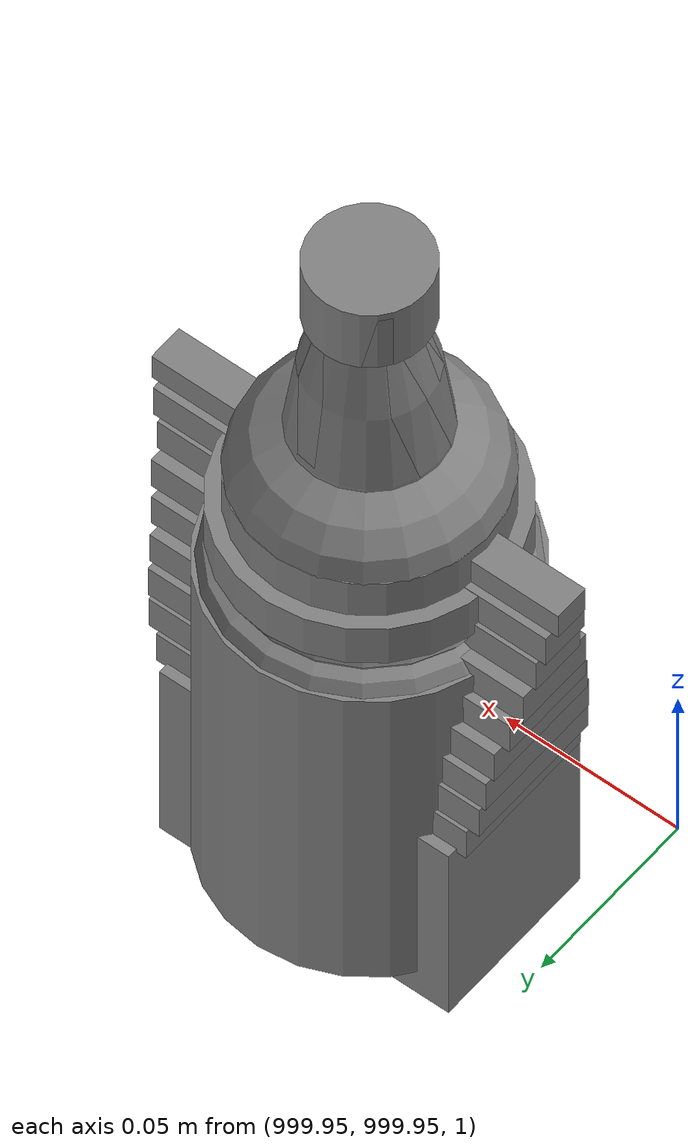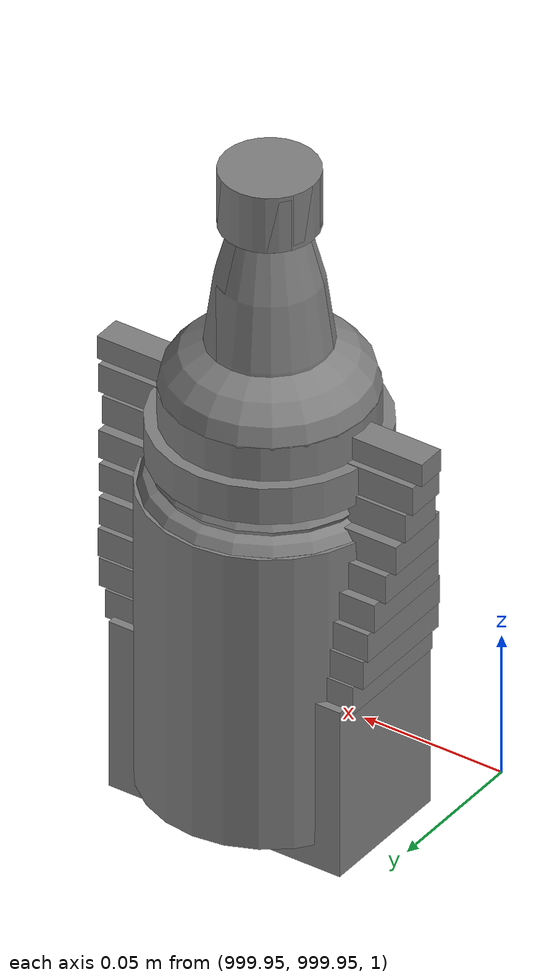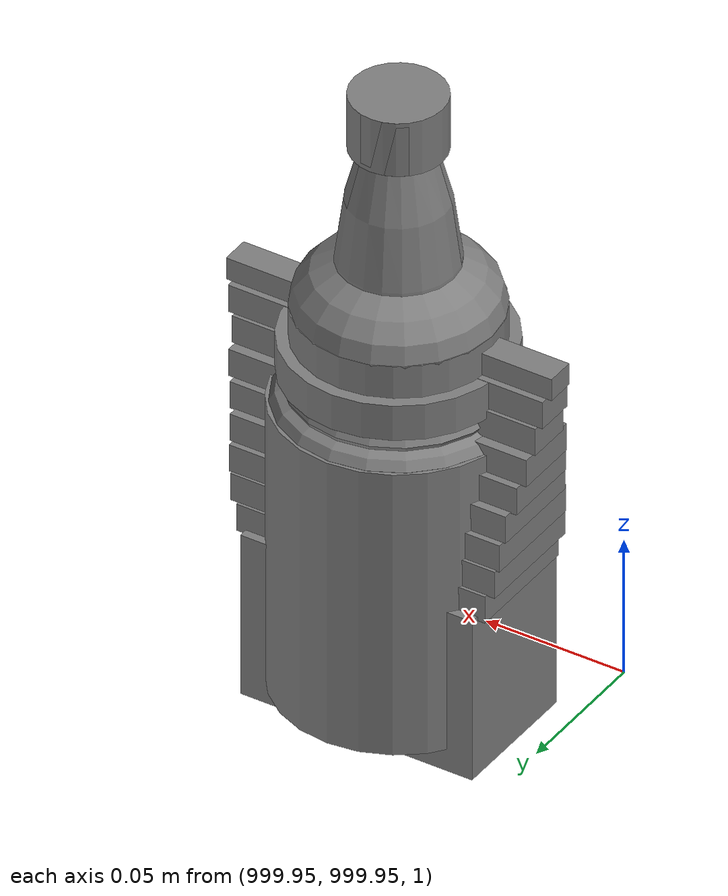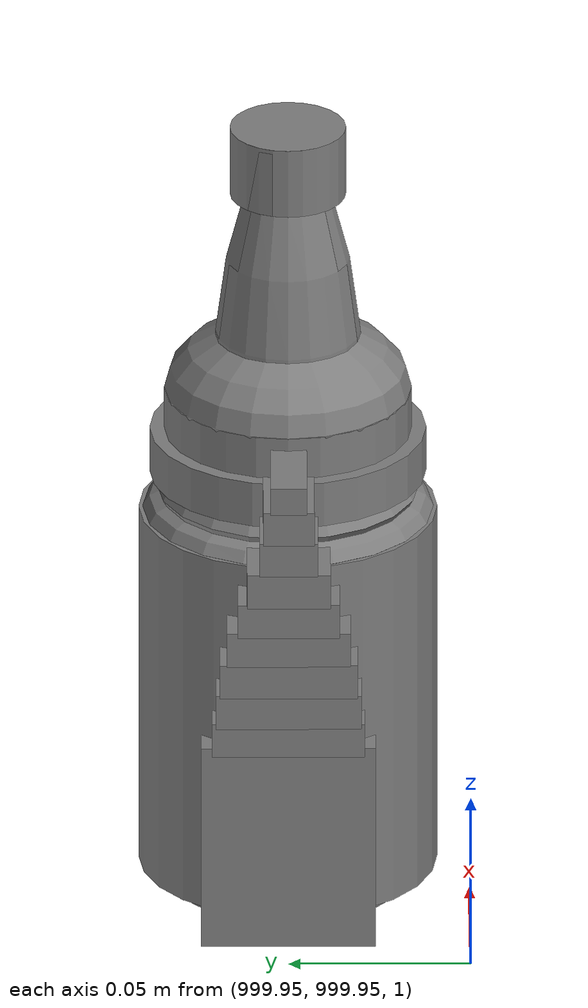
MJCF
<mujoco>
    <option gravity="0.000000000 0.000000000 -9.810000420" timestep="0.0166666" integrator="implicitfast" density="1.225" viscosity="1.8000001e-05" noslip_iterations="10" iterations="100" sdf_iterations="50">
        <flag multiccd="disable"/>
    </option>
    <size memory="1000M"/>
    <compiler coordinate="local"/>
    <worldbody>
        <light cutoff="30" pos="0 1 1" dir="0 -1 -2"/>
        <light cutoff="30" pos="0 -1 1" dir="0 1 -2"/>
        <body pos="0.000000000 0.000000000 0.000000000" euler="0.000000000 0.000000000 0.000000000" name=" Static Objects_ Static Objects">
            <geom contype="1" conaffinity="1" density="1000" type="box" material="" rgba="0.500000000 0.500000000 0.500000000 1.000000000" solimp="0.899999976 0.949999988 0.001000000" friction="1.000000000 0.005000000 0.000100000" solref="0.020000000 1.000000000" margin="0" condim="3" group="0" pos="-3.101639986 6.150595188 1.018643856" quat="1.000000000 0.000000000 0.000000000 0.000000000" size="0.050000001 0.579999983 1.019999981" name=" Static Objects_geom_B0224666_2C5B_424B_B6E4_1B9E4215C01C"/>
            <geom contype="1" conaffinity="1" density="1000" type="box" material="" rgba="0.500000000 0.500000000 0.500000000 1.000000000" solimp="0.899999976 0.949999988 0.001000000" friction="1.000000000 0.005000000 0.000100000" solref="0.020000000 1.000000000" margin="0" condim="3" group="0" pos="-2.825197220 6.153595448 1.115278244" quat="0.707107067 0.000000000 0.000000000 0.707106471" size="0.550000012 0.239999995 0.025000000" name=" Static Objects_geom_81F1BE10_B464_4F22_A741_64DD710321C9"/>
            <geom contype="1" conaffinity="1" density="1000" type="box" material="" rgba="0.500000000 0.500000000 0.500000000 1.000000000" solimp="0.899999976 0.949999988 0.001000000" friction="1.000000000 0.005000000 0.000100000" solref="0.020000000 1.000000000" margin="0" condim="3" group="0" pos="-2.825197220 6.153595448 0.097434282" quat="0.707107067 0.000000000 0.000000000 0.707106471" size="0.550000012 0.239999995 0.098999999" name=" Static Objects_geom_E39E48DE_AB50_4DA0_934E_EE72C068C190"/>
            <geom contype="1" conaffinity="1" density="1000" type="box" material="" rgba="0.500000000 0.500000000 0.500000000 1.000000000" solimp="0.899999976 0.949999988 0.001000000" friction="1.000000000 0.005000000 0.000100000" solref="0.020000000 1.000000000" margin="0" condim="3" group="0" pos="-6.293097973 6.153595448 1.114443064" quat="0.707107067 0.000000000 0.000000000 0.707106471" size="0.529999971 3.134999990 0.025000000" name=" Static Objects_geom_32F50217_D7EF_4823_8B3B_3CFCFCBD1BA5"/>
            <geom contype="1" conaffinity="1" density="1000" type="box" material="" rgba="0.500000000 0.500000000 0.500000000 1.000000000" solimp="0.899999976 0.949999988 0.001000000" friction="1.000000000 0.005000000 0.000100000" solref="0.020000000 1.000000000" margin="0" condim="3" group="0" pos="-6.286010742 6.153595448 0.096129179" quat="0.707107067 0.000000000 0.000000000 0.707106471" size="0.529999971 3.134999990 0.098999999" name=" Static Objects_geom_A22511DB_BBF3_482D_A32F_B812323ADD3E"/>
            <geom contype="1" conaffinity="1" density="1000" type="box" material="" rgba="0.500000000 0.500000000 0.500000000 1.000000000" solimp="0.899999976 0.949999988 0.001000000" friction="1.000000000 0.005000000 0.000100000" solref="0.020000000 1.000000000" margin="0" condim="3" group="0" pos="-2.825197220 6.153595448 1.563861728" quat="0.707107067 0.000000000 0.000000000 0.707106471" size="0.550000012 0.239999995 0.025000000" name=" Static Objects_geom_C41D093D_C942_4E44_8FCC_1A50414D60AA"/>
            <geom contype="1" conaffinity="1" density="1000" type="box" material="" rgba="0.500000000 0.500000000 0.500000000 1.000000000" solimp="0.899999976 0.949999988 0.001000000" friction="1.000000000 0.005000000 0.000100000" solref="0.020000000 1.000000000" margin="0" condim="3" group="0" pos="-6.311686516 6.153595448 1.018643856" quat="0.707107067 0.000000000 0.000000000 0.707106471" size="0.050000001 3.150000095 1.019999981" name=" Static Objects_geom_74CBFFAE_5601_4A2A_9C4D_D8D00A77ABA5"/>
            <geom contype="1" conaffinity="1" density="1000" type="box" material="" rgba="0.500000000 0.500000000 0.500000000 1.000000000" solimp="0.899999976 0.949999988 0.001000000" friction="1.000000000 0.005000000 0.000100000" solref="0.020000000 1.000000000" margin="0" condim="3" group="0" pos="-2.825197220 6.153595448 0.629031777" quat="0.707107067 0.000000000 0.000000000 0.707106471" size="0.550000012 0.239999995 0.025000000" name=" Static Objects_geom_DC92D274_13BD_4045_937C_6598E6812CE4"/>
            <geom contype="1" conaffinity="1" density="1000" type="box" material="" rgba="0.500000000 0.500000000 0.500000000 1.000000000" solimp="0.899999976 0.949999988 0.001000000" friction="1.000000000 0.005000000 0.000100000" solref="0.020000000 1.000000000" margin="0" condim="3" group="0" pos="-6.286010742 6.153595448 1.563861728" quat="0.707107067 0.000000000 0.000000000 0.707106471" size="0.529999971 3.134999990 0.025000000" name=" Static Objects_geom_9C21B7D2_4767_4568_967F_F4846A6B4E91"/>
            <geom contype="1" conaffinity="1" density="1000" type="box" material="" rgba="0.500000000 0.500000000 0.500000000 1.000000000" solimp="0.899999976 0.949999988 0.001000000" friction="1.000000000 0.005000000 0.000100000" solref="0.020000000 1.000000000" margin="0" condim="3" group="0" pos="-6.286010742 6.153595448 0.629031777" quat="0.707107067 0.000000000 0.000000000 0.707106471" size="0.529999971 3.134999990 0.025000000" name=" Static Objects_geom_A4A41A8B_6A8A_4546_B0BB_22C7186A538A"/>
            <geom contype="1" conaffinity="1" density="1000" type="box" material="" rgba="0.500000000 0.500000000 0.500000000 1.000000000" solimp="0.899999976 0.949999988 0.001000000" friction="1.000000000 0.005000000 0.000100000" solref="0.020000000 1.000000000" margin="0" condim="3" group="0" pos="-7.719123363 2.867671013 1.173410416" quat="1.000000000 0.000000000 0.000000000 0.000000000" size="0.250000000 0.250000000 0.079999998" name=" Static Objects_geom_CCBCA029_9AA9_4F2B_B0DF_F6471C9F2D3B"/>
            <geom contype="1" conaffinity="1" density="1000" type="box" material="" rgba="0.500000000 0.500000000 0.500000000 1.000000000" solimp="0.899999976 0.949999988 0.001000000" friction="1.000000000 0.005000000 0.000100000" solref="0.020000000 1.000000000" margin="0" condim="3" group="0" pos="-7.408766270 3.088089943 1.776644945" quat="0.928051054 0.000000000 0.000000000 0.372453064" size="0.050000001 0.100000001 0.050000001" name=" Static Objects_geom_39DDCD1A_7400_4771_A57E_86CFBEBFA191"/>
            <geom contype="1" conaffinity="1" density="1000" type="box" material="" rgba="0.500000000 0.500000000 0.500000000 1.000000000" solimp="0.899999976 0.949999988 0.001000000" friction="1.000000000 0.005000000 0.000100000" solref="0.020000000 1.000000000" margin="0" condim="3" group="0" pos="-7.719123363 2.958004713 1.530241251" quat="1.000000000 0.000000000 0.000000000 0.000000000" size="0.250000000 0.159999996 0.280000001" name=" Static Objects_geom_9B5047D9_65F9_4C20_A05B_55971362B1BC"/>
            <geom contype="1" conaffinity="1" density="1000" type="cylinder" material="" rgba="0.500000000 0.500000000 0.500000000 1.000000000" solimp="0.899999976 0.949999988 0.001000000" friction="1.000000000 0.005000000 0.000100000" solref="0.020000000 1.000000000" margin="0" condim="3" group="0" pos="-7.427312374 3.069516420 1.502544641" quat="0.928051054 0.000000000 0.000000000 0.372453064" size="0.015000000 0.230000004 0.100000001" name=" Static Objects_geom_2BA6521B_E1A7_45A0_B25A_8055CA1CA7D5"/>
            <geom contype="1" conaffinity="1" density="1000" type="box" material="" rgba="0.500000000 0.500000000 0.500000000 1.000000000" solimp="0.899999976 0.949999988 0.001000000" friction="1.000000000 0.005000000 0.000100000" solref="0.020000000 1.000000000" margin="0" condim="3" group="0" pos="-7.437745571 3.067511320 1.289965630" quat="1.000000000 0.000000000 0.000000000 0.000000000" size="0.029999999 0.020000000 0.020000000" name=" Static Objects_geom_81FBA1D6_2E45_414E_AA12_10B6D9A7E7AE"/>
            <geom contype="1" conaffinity="1" density="1000" type="box" material="" rgba="0.500000000 0.500000000 0.500000000 1.000000000" solimp="0.899999976 0.949999988 0.001000000" friction="1.000000000 0.005000000 0.000100000" solref="0.020000000 1.000000000" margin="0" condim="3" group="0" pos="-9.058088303 6.434794426 1.209077358" quat="1.000000000 0.000000000 0.000000000 0.000000000" size="0.250000000 0.100000001 0.070000000" name=" Static Objects_geom_133F10A9_DCAD_451E_9DED_5F94E56033AE"/>
            <geom contype="1" conaffinity="1" density="1000" type="box" material="" rgba="0.500000000 0.500000000 0.500000000 1.000000000" solimp="0.899999976 0.949999988 0.001000000" friction="1.000000000 0.005000000 0.000100000" solref="0.020000000 1.000000000" margin="0" condim="3" group="0" pos="-7.886891365 6.459744930 0.352518857" quat="1.000000000 0.000000000 0.000000000 0.000000000" size="1.500000000 0.200000003 0.150000006" name=" Static Objects_geom_15F14E26_92B0_4424_9145_D6F1E7E83D4A"/>
            <geom contype="1" conaffinity="1" density="1000" type="box" material="" rgba="0.500000000 0.500000000 0.500000000 1.000000000" solimp="0.899999976 0.949999988 0.001000000" friction="1.000000000 0.005000000 0.000100000" solref="0.020000000 1.000000000" margin="0" condim="3" group="0" pos="-9.237723351 6.464855671 1.209077358" quat="1.000000000 0.000000000 0.000000000 0.000000000" size="0.100000001 0.100000001 0.070000000" name=" Static Objects_geom_88CBDF71_1674_4994_89D2_F2B05FAD2E65"/>
            <geom contype="1" conaffinity="1" density="1000" type="box" material="" rgba="0.500000000 0.500000000 0.500000000 1.000000000" solimp="0.899999976 0.949999988 0.001000000" friction="1.000000000 0.005000000 0.000100000" solref="0.020000000 1.000000000" margin="0" condim="3" group="0" pos="-6.924745083 6.362090111 1.214329123" quat="1.000000000 0.000000000 0.000000000 0.000000000" size="0.200000003 0.100000001 0.075000003" name=" Static Objects_geom_E4B251A8_497D_403E_A948_FF2B958FEF37"/>
            <geom contype="1" conaffinity="1" density="1000" type="box" material="" rgba="0.500000000 0.500000000 0.500000000 1.000000000" solimp="0.899999976 0.949999988 0.001000000" friction="1.000000000 0.005000000 0.000100000" solref="0.020000000 1.000000000" margin="0" condim="3" group="0" pos="-4.407354832 6.459744930 1.292199373" quat="1.000000000 0.000000000 0.000000000 0.000000000" size="1.240000010 0.200000003 0.150000006" name=" Static Objects_geom_B15A33DE_28D8_4006_A0DC_130A2BE05FAE"/>
            <geom contype="1" conaffinity="1" density="1000" type="box" material="" rgba="0.500000000 0.500000000 0.500000000 1.000000000" solimp="0.899999976 0.949999988 0.001000000" friction="1.000000000 0.005000000 0.000100000" solref="0.020000000 1.000000000" margin="0" condim="3" group="0" pos="-5.611940861 6.318420410 0.350975692" quat="1.000000000 0.000000000 0.000000000 0.000000000" size="0.699999988 0.100000001 0.150000006" name=" Static Objects_geom_C3E53777_B1DE_4592_805B_68555D9A345F"/>
            <geom contype="1" conaffinity="1" density="1000" type="box" material="" rgba="0.500000000 0.500000000 0.500000000 1.000000000" solimp="0.899999976 0.949999988 0.001000000" friction="1.000000000 0.005000000 0.000100000" solref="0.020000000 1.000000000" margin="0" condim="3" group="0" pos="-6.300771236 6.459744930 1.744376063" quat="1.000000000 0.000000000 0.000000000 0.000000000" size="3.000000000 0.200000003 0.150000006" name=" Static Objects_geom_8ED553B1_6D89_4059_9D99_79288225810B"/>
            <geom contype="1" conaffinity="1" density="1000" type="box" material="" rgba="0.500000000 0.500000000 0.500000000 1.000000000" solimp="0.899999976 0.949999988 0.001000000" friction="1.000000000 0.005000000 0.000100000" solref="0.020000000 1.000000000" margin="0" condim="3" group="0" pos="-6.751636982 6.459744930 0.800981164" quat="1.000000000 0.000000000 0.000000000 0.000000000" size="2.200000048 0.200000003 0.150000006" name=" Static Objects_geom_2D01B982_26A5_44E8_9DA3_6CEF9CDD9CF4"/>
            <geom contype="1" conaffinity="1" density="1000" type="box" material="" rgba="0.500000000 0.500000000 0.500000000 1.000000000" solimp="0.899999976 0.949999988 0.001000000" friction="1.000000000 0.005000000 0.000100000" solref="0.020000000 1.000000000" margin="0" condim="3" group="0" pos="-8.844120979 6.464855671 1.209077358" quat="1.000000000 0.000000000 0.000000000 0.000000000" size="0.100000001 0.100000001 0.070000000" name=" Static Objects_geom_2CB9504F_0ACC_4B10_AC7E_7FF612A60899"/>
            <geom contype="1" conaffinity="1" density="1000" type="box" material="" rgba="0.500000000 0.500000000 0.500000000 1.000000000" solimp="0.899999976 0.949999988 0.001000000" friction="1.000000000 0.005000000 0.000100000" solref="0.020000000 1.000000000" margin="0" condim="3" group="0" pos="-6.098561764 6.327973843 1.292199373" quat="1.000000000 0.000000000 0.000000000 0.000000000" size="0.500000000 0.100000001 0.150000006" name=" Static Objects_geom_E973C1D0_AF5C_47DF_B622_F67DDC69043C"/>
            <geom contype="1" conaffinity="1" density="1000" type="box" material="" rgba="0.500000000 0.500000000 0.500000000 1.000000000" solimp="0.899999976 0.949999988 0.001000000" friction="1.000000000 0.005000000 0.000100000" solref="0.020000000 1.000000000" margin="0" condim="3" group="0" pos="-6.824534416 6.447464466 1.212718010" quat="1.000000000 0.000000000 0.000000000 0.000000000" size="0.100000001 0.100000001 0.075000003" name=" Static Objects_geom_129F4B03_1B7C_4CF6_965C_E70F6BC1D2DF"/>
            <geom contype="1" conaffinity="1" density="1000" type="box" material="" rgba="0.500000000 0.500000000 0.500000000 1.000000000" solimp="0.899999976 0.949999988 0.001000000" friction="1.000000000 0.005000000 0.000100000" solref="0.020000000 1.000000000" margin="0" condim="3" group="0" pos="-3.907610416 6.318625927 0.800981164" quat="1.000000000 0.000000000 0.000000000 0.000000000" size="0.500000000 0.100000001 0.150000006" name=" Static Objects_geom_56EDB44D_77C7_408E_89E7_E100DF95BC94"/>
            <geom contype="1" conaffinity="1" density="1000" type="box" material="" rgba="0.500000000 0.500000000 0.500000000 1.000000000" solimp="0.899999976 0.949999988 0.001000000" friction="1.000000000 0.005000000 0.000100000" solref="0.020000000 1.000000000" margin="0" condim="3" group="0" pos="-7.373087406 6.458900928 1.214329123" quat="1.000000000 0.000000000 0.000000000 0.000000000" size="0.250000000 0.200000003 0.075000003" name=" Static Objects_geom_CB616015_F4B4_42C0_8544_B66FDFEAFD12"/>
            <geom contype="1" conaffinity="1" density="1000" type="box" material="" rgba="0.500000000 0.500000000 0.500000000 1.000000000" solimp="0.899999976 0.949999988 0.001000000" friction="1.000000000 0.005000000 0.000100000" solref="0.020000000 1.000000000" margin="0" condim="3" group="0" pos="-4.035642624 6.459744930 0.352518857" quat="1.000000000 0.000000000 0.000000000 0.000000000" size="0.800000012 0.200000003 0.150000006" name=" Static Objects_geom_3D012B93_8209_4468_9742_E2B624FF88F9"/>
            <geom contype="1" conaffinity="1" density="1000" type="box" material="" rgba="0.500000000 0.500000000 0.500000000 1.000000000" solimp="0.899999976 0.949999988 0.001000000" friction="1.000000000 0.005000000 0.000100000" solref="0.020000000 1.000000000" margin="0" condim="3" group="0" pos="-6.460197449 2.937205315 0.548931718" quat="1.000000000 0.000000000 0.000000000 0.000000000" size="2.650000095 0.430000007 0.550000012" name=" Static Objects_geom_11009601_DD9D_46D0_9E67_8B5CBA469CDC"/>
            <geom contype="1" conaffinity="1" density="1000" type="box" material="" rgba="0.500000000 0.500000000 0.500000000 1.000000000" solimp="0.899999976 0.949999988 0.001000000" friction="1.000000000 0.005000000 0.000100000" solref="0.020000000 1.000000000" margin="0" condim="3" group="0" pos="-4.240264893 1.327049494 0.549888909" quat="1.000000000 0.000000000 0.000000000 0.000000000" size="0.430000007 1.200000048 0.550000012" name=" Static Objects_geom_1A3671FB_66DA_4619_ADA4_44695F71B3D1"/>
            <geom contype="1" conaffinity="1" density="1000" type="box" material="" rgba="0.500000000 0.500000000 0.500000000 1.000000000" solimp="0.899999976 0.949999988 0.001000000" friction="1.000000000 0.005000000 0.000100000" solref="0.020000000 1.000000000" margin="0" condim="3" group="0" pos="-8.830721855 2.096410990 0.549305558" quat="1.000000000 0.000000000 0.000000000 0.000000000" size="0.280000001 0.430000007 0.550000012" name=" Static Objects_geom_C722F0FE_A6DA_4B7F_A142_2B9CCB8715F7"/>
            <geom contype="1" conaffinity="1" density="1000" type="plane" material="" rgba="0.500000000 0.500000000 0.500000000 1.000000000" solimp="0.899999976 0.949999988 0.001000000" friction="1.000000000 0.005000000 0.000100000" solref="0.020000000 1.000000000" margin="0" condim="3" group="0" pos="-6.000000000 10.399999619 0.000000000" quat="1.000000000 0.000000000 0.000000000 0.000000000" size="6.050000191 10.800000191 0.010000000" name=" Static Objects_geom_FF938707_0BF3_4875_AFD1_643CC8D55ADD"/>
            <geom contype="1" conaffinity="1" density="1000" type="box" material="" rgba="0.500000000 0.500000000 0.500000000 1.000000000" solimp="0.899999976 0.949999988 0.001000000" friction="1.000000000 0.005000000 0.000100000" solref="0.020000000 1.000000000" margin="0" condim="3" group="0" pos="-6.000000000 0.035000000 2.000000000" quat="1.000000000 0.000000000 0.000000000 0.000000000" size="6.079999924 0.070000000 2.000000000" name=" Static Objects_geom_45F12B17_9800_4F5D_8AB4_535B3B29D542"/>
            <geom contype="1" conaffinity="1" density="1000" type="box" material="" rgba="0.500000000 0.500000000 0.500000000 1.000000000" solimp="0.899999976 0.949999988 0.001000000" friction="1.000000000 0.005000000 0.000100000" solref="0.020000000 1.000000000" margin="0" condim="3" group="0" pos="-6.000000000 20.159999847 2.000000000" quat="1.000000000 0.000000000 0.000000000 0.000000000" size="6.079999924 0.070000000 2.000000000" name=" Static Objects_geom_FC0768A6_A0E9_49BC_9AF9_B8B922ADBA1C"/>
            <geom contype="1" conaffinity="1" density="1000" type="box" material="" rgba="0.500000000 0.500000000 0.500000000 1.000000000" solimp="0.899999976 0.949999988 0.001000000" friction="1.000000000 0.005000000 0.000100000" solref="0.020000000 1.000000000" margin="0" condim="3" group="0" pos="0.000000000 10.000000000 2.000000000" quat="1.000000000 0.000000000 0.000000000 0.000000000" size="0.070000000 10.500000000 2.000000000" name=" Static Objects_geom_120F3924_3C38_4612_B21B_C80B9E0E6C13"/>
            <geom contype="1" conaffinity="1" density="1000" type="box" material="" rgba="0.500000000 0.500000000 0.500000000 1.000000000" solimp="0.899999976 0.949999988 0.001000000" friction="1.000000000 0.005000000 0.000100000" solref="0.020000000 1.000000000" margin="0" condim="3" group="0" pos="-12.050000191 10.000000000 2.000000000" quat="1.000000000 0.000000000 0.000000000 0.000000000" size="0.070000000 10.500000000 2.000000000" name=" Static Objects_geom_9883472E_89D2_4EA4_AFFC_51BBD45F6E6F"/>
        </body>
        <body pos="1000.000000000 1000.000000000 1.000000000" euler="0.000000000 0.000000000 0.000000000" name="openloong_gripper_2f85_fix_base_usda_bottle_red">
            <geom contype="1" conaffinity="1" density="1000" type="ellipsoid" material="" rgba="0.500000000 0.500000000 0.500000000 1.000000000" solimp="0.899999976 0.949999988 0.001000000" friction="1.000000000 0.005000000 0.000100000" solref="0.020000000 1.000000000" margin="0" condim="3" group="0" pos="0.000000000 0.000000000 0.144284487" quat="1.000000000 0.000000000 0.000000000 0.000000000" size="0.021000000 0.021000000 0.079999998" name="openloong_gripper_2f85_fix_base_usda_geom_9AF45DB0_AFB4_44A6_BB6E_4B8A4B0F146E"/>
            <geom contype="1" conaffinity="1" density="1000" type="cylinder" material="" rgba="0.500000000 0.500000000 0.500000000 1.000000000" solimp="0.899999976 0.949999988 0.001000000" friction="1.000000000 0.005000000 0.000100000" solref="0.020000000 1.000000000" margin="0" condim="3" group="0" pos="0.000000000 0.000000000 0.220618963" quat="1.000000000 0.000000000 0.000000000 0.000000000" size="0.016000001 0.010000000 1.000000000" name="openloong_gripper_2f85_fix_base_usda_geom_79EBD640_1758_4B3D_BC48_DEBA87D7DCB8"/>
            <geom contype="1" conaffinity="1" density="1000" type="ellipsoid" material="" rgba="0.500000000 0.500000000 0.500000000 1.000000000" solimp="0.899999976 0.949999988 0.001000000" friction="1.000000000 0.005000000 0.000100000" solref="0.020000000 1.000000000" margin="0" condim="3" group="0" pos="0.000000000 0.000000000 0.118945479" quat="1.000000000 0.000000000 0.000000000 0.000000000" size="0.030999999 0.030999999 0.029999999" name="openloong_gripper_2f85_fix_base_usda_geom_EEE55DA2_18E1_4A88_BD7E_C44F78E8F5B8"/>
            <geom contype="1" conaffinity="1" density="1000" type="box" material="" rgba="0.500000000 0.500000000 0.500000000 1.000000000" solimp="0.899999976 0.949999988 0.001000000" friction="1.000000000 0.005000000 0.000100000" solref="0.020000000 1.000000000" margin="0" condim="3" group="0" pos="0.000000000 0.000000000 0.002189159" quat="1.000000000 0.000000000 0.000000000 0.000000000" size="0.020000000 0.020000000 0.003000000" name="openloong_gripper_2f85_fix_base_usda_geom_12F94D4A_2585_4A53_9216_0EF7CC966881"/>
            <geom contype="1" conaffinity="1" density="1000" type="cylinder" material="" rgba="0.500000000 0.500000000 0.500000000 1.000000000" solimp="0.899999976 0.949999988 0.001000000" friction="1.000000000 0.005000000 0.000100000" solref="0.020000000 1.000000000" margin="0" condim="3" group="0" pos="0.000000000 -0.000366211 0.060884237" quat="1.000000000 0.000000000 0.000000000 0.000000000" size="0.030999999 0.057999998 1.000000000" name="openloong_gripper_2f85_fix_base_usda_geom_8E83354E_919E_4FE4_87D7_C5C21814FDDA"/>
            <freejoint name="openloong_gripper_2f85_fix_base_usda_bottle_red_joint"/>
            <site size="0.005000000 0.005000000 0.005000000" rgba="0.500000000 0.500000000 0.500000000 1.000000000" pos="0.000000000 0.000000000 0.000000000" quat="0.999961913 0.008726535 0.000000000 0.000000000" group="0" type="sphere" name="openloong_gripper_2f85_fix_base_usda_bottle_redsite"/>
        </body>
        <body pos="-2.270662069 6.477569103 1.784165144" euler="65.260589600 24.065149307 -59.379585266" mocap="true" name="spotlight4_SpotLight"/>
        <body pos="-2.300213337 6.265947342 1.856889844" euler="-123.496124268 -21.176836014 91.237663269" mocap="true" name="spotlight6_SpotLight"/>
        <body pos="1000.000000000 1000.000000000 1.000000000" euler="0.000000000 0.000000000 0.000000000" name="openloong_gripper_2f85_fix_base_usda_bottle_blue">
            <geom contype="1" conaffinity="1" density="1000" type="ellipsoid" material="" rgba="0.500000000 0.500000000 0.500000000 1.000000000" solimp="0.899999976 0.949999988 0.001000000" friction="1.000000000 0.005000000 0.000100000" solref="0.020000000 1.000000000" margin="0" condim="3" group="0" pos="0.000000000 0.000000000 0.118920922" quat="1.000000000 0.000000000 0.000000000 0.000000000" size="0.030999999 0.030999999 0.029999999" name="openloong_gripper_2f85_fix_base_usda_geom_F6870D7E_D2CF_4394_9F04_B125E47A9CCC"/>
            <geom contype="1" conaffinity="1" density="1000" type="box" material="" rgba="0.500000000 0.500000000 0.500000000 1.000000000" solimp="0.899999976 0.949999988 0.001000000" friction="1.000000000 0.005000000 0.000100000" solref="0.020000000 1.000000000" margin="0" condim="3" group="0" pos="0.000000000 0.000000000 0.002164602" quat="1.000000000 0.000000000 0.000000000 0.000000000" size="0.020000000 0.020000000 0.003000000" name="openloong_gripper_2f85_fix_base_usda_geom_857001A9_E2D9_41FC_83E2_1CC2D9CC057F"/>
            <geom contype="1" conaffinity="1" density="1000" type="cylinder" material="" rgba="0.500000000 0.500000000 0.500000000 1.000000000" solimp="0.899999976 0.949999988 0.001000000" friction="1.000000000 0.005000000 0.000100000" solref="0.020000000 1.000000000" margin="0" condim="3" group="0" pos="0.000000000 -0.000366211 0.060859680" quat="1.000000000 0.000000000 0.000000000 0.000000000" size="0.030999999 0.057999998 1.000000000" name="openloong_gripper_2f85_fix_base_usda_geom_D3A01FF8_FCF6_4C78_A547_8E930574C723"/>
            <geom contype="1" conaffinity="1" density="1000" type="cylinder" material="" rgba="0.500000000 0.500000000 0.500000000 1.000000000" solimp="0.899999976 0.949999988 0.001000000" friction="1.000000000 0.005000000 0.000100000" solref="0.020000000 1.000000000" margin="0" condim="3" group="0" pos="0.000000000 0.000000000 0.220594406" quat="1.000000000 0.000000000 0.000000000 0.000000000" size="0.016000001 0.010000000 1.000000000" name="openloong_gripper_2f85_fix_base_usda_geom_ACE60A2E_1AAE_4D6B_AD2C_6AE3B71ED0A1"/>
            <geom contype="1" conaffinity="1" density="1000" type="ellipsoid" material="" rgba="0.500000000 0.500000000 0.500000000 1.000000000" solimp="0.899999976 0.949999988 0.001000000" friction="1.000000000 0.005000000 0.000100000" solref="0.020000000 1.000000000" margin="0" condim="3" group="0" pos="0.000000000 0.000000000 0.144259930" quat="1.000000000 0.000000000 0.000000000 0.000000000" size="0.021000000 0.021000000 0.079999998" name="openloong_gripper_2f85_fix_base_usda_geom_61B04C1D_A4C6_4915_8F47_66881D1BE4C0"/>
            <freejoint name="openloong_gripper_2f85_fix_base_usda_bottle_blue_joint"/>
            <site size="0.005000000 0.005000000 0.005000000" rgba="0.500000000 0.500000000 0.500000000 1.000000000" pos="0.000000000 0.000000000 0.000000000" quat="0.999961913 0.008726535 0.000000000 0.000000000" group="0" type="sphere" name="openloong_gripper_2f85_fix_base_usda_bottle_bluesite"/>
        </body>
        <body pos="-1.995493770 6.236029625 1.835561633" euler="11.387240410 57.109653473 -107.811447144" mocap="true" name="spotlight1_SpotLight"/>
        <body pos="1000.000000000 1000.000000000 1.000000000" euler="0.000000000 0.000000000 0.000000000" name="openloong_gripper_2f85_fix_base_usda_salt">
            <geom contype="1" conaffinity="1" density="1000" type="box" material="" rgba="0.500000000 0.500000000 0.500000000 1.000000000" solimp="0.899999976 0.949999988 0.001000000" friction="1.000000000 0.005000000 0.000100000" solref="0.020000000 1.000000000" margin="0" condim="3" group="0" pos="0.000305176 0.000000000 0.084862232" quat="1.000000000 0.000000000 0.000000000 0.000000000" size="0.048999999 0.018999999 0.005000000" name="openloong_gripper_2f85_fix_base_usda_geom_4A7ADDAD_3BFA_4BBD_B001_E5A516CA7B10"/>
            <geom contype="1" conaffinity="1" density="1000" type="box" material="" rgba="0.500000000 0.500000000 0.500000000 1.000000000" solimp="0.899999976 0.949999988 0.001000000" friction="1.000000000 0.005000000 0.000100000" solref="0.020000000 1.000000000" margin="0" condim="3" group="0" pos="0.000305176 0.000000000 0.104564309" quat="1.000000000 0.000000000 0.000000000 0.000000000" size="0.052000001 0.014000000 0.005000000" name="openloong_gripper_2f85_fix_base_usda_geom_E9D55100_E3EF_4282_BAB8_3A424C37F839"/>
            <geom contype="1" conaffinity="1" density="1000" type="box" material="" rgba="0.500000000 0.500000000 0.500000000 1.000000000" solimp="0.899999976 0.949999988 0.001000000" friction="1.000000000 0.005000000 0.000100000" solref="0.020000000 1.000000000" margin="0" condim="3" group="0" pos="0.000305176 0.000000000 0.114487171" quat="1.000000000 0.000000000 0.000000000 0.000000000" size="0.054000001 0.011500000 0.005000000" name="openloong_gripper_2f85_fix_base_usda_geom_2B2BCAE2_D4D9_4BE3_8EF3_15ACC7C036EF"/>
            <geom contype="1" conaffinity="1" density="1000" type="box" material="" rgba="0.500000000 0.500000000 0.500000000 1.000000000" solimp="0.899999976 0.949999988 0.001000000" friction="1.000000000 0.005000000 0.000100000" solref="0.020000000 1.000000000" margin="0" condim="3" group="0" pos="0.000305176 0.000000000 0.075103164" quat="1.000000000 0.000000000 0.000000000 0.000000000" size="0.048000000 0.020000000 0.005000000" name="openloong_gripper_2f85_fix_base_usda_geom_9585DD2D_1CA9_4401_8722_98816B5DD290"/>
            <geom contype="1" conaffinity="1" density="1000" type="box" material="" rgba="0.500000000 0.500000000 0.500000000 1.000000000" solimp="0.899999976 0.949999988 0.001000000" friction="1.000000000 0.005000000 0.000100000" solref="0.020000000 1.000000000" margin="0" condim="3" group="0" pos="0.000305176 0.000000000 0.134892464" quat="1.000000000 0.000000000 0.000000000 0.000000000" size="0.057000000 0.007000000 0.005000000" name="openloong_gripper_2f85_fix_base_usda_geom_EBF743D2_A82A_4096_9BFE_6179727C67E4"/>
            <geom contype="1" conaffinity="1" density="1000" type="box" material="" rgba="0.500000000 0.500000000 0.500000000 1.000000000" solimp="0.899999976 0.949999988 0.001000000" friction="1.000000000 0.005000000 0.000100000" solref="0.020000000 1.000000000" margin="0" condim="3" group="0" pos="0.000305176 0.000000000 0.094920278" quat="1.000000000 0.000000000 0.000000000 0.000000000" size="0.050000001 0.017000001 0.005000000" name="openloong_gripper_2f85_fix_base_usda_geom_0F668476_1E1F_4AE9_9234_C2F4F06F1DB3"/>
            <geom contype="1" conaffinity="1" density="1000" type="box" material="" rgba="0.500000000 0.500000000 0.500000000 1.000000000" solimp="0.899999976 0.949999988 0.001000000" friction="1.000000000 0.005000000 0.000100000" solref="0.020000000 1.000000000" margin="0" condim="3" group="0" pos="0.000305176 0.000000000 0.065204859" quat="1.000000000 0.000000000 0.000000000 0.000000000" size="0.045000002 0.021000000 0.005000000" name="openloong_gripper_2f85_fix_base_usda_geom_5936E5BA_3064_43F1_A151_5F812CEB0817"/>
            <geom contype="1" conaffinity="1" density="1000" type="box" material="" rgba="0.500000000 0.500000000 0.500000000 1.000000000" solimp="0.899999976 0.949999988 0.001000000" friction="1.000000000 0.005000000 0.000100000" solref="0.020000000 1.000000000" margin="0" condim="3" group="0" pos="0.000305176 0.000000000 0.144135714" quat="1.000000000 0.000000000 0.000000000 0.000000000" size="0.059000000 0.005000000 0.004000000" name="openloong_gripper_2f85_fix_base_usda_geom_38F9C180_89B5_4937_A81D_431560AD2C32"/>
            <geom contype="1" conaffinity="1" density="1000" type="box" material="" rgba="0.500000000 0.500000000 0.500000000 1.000000000" solimp="0.899999976 0.949999988 0.001000000" friction="1.000000000 0.005000000 0.000100000" solref="0.020000000 1.000000000" margin="0" condim="3" group="0" pos="0.000000000 0.000000000 0.031593561" quat="1.000000000 0.000000000 0.000000000 0.000000000" size="0.041999999 0.024000000 0.029999999" name="openloong_gripper_2f85_fix_base_usda_geom_36836EE0_F4C3_46F6_91B1_6BD02D8D4BA3"/>
            <geom contype="1" conaffinity="1" density="1000" type="box" material="" rgba="0.500000000 0.500000000 0.500000000 1.000000000" solimp="0.899999976 0.949999988 0.001000000" friction="1.000000000 0.005000000 0.000100000" solref="0.020000000 1.000000000" margin="0" condim="3" group="0" pos="0.000305176 0.000000000 0.124608755" quat="1.000000000 0.000000000 0.000000000 0.000000000" size="0.055000000 0.008000000 0.005000000" name="openloong_gripper_2f85_fix_base_usda_geom_F244B1F0_8BFC_4453_91E8_3AEE6E0ED172"/>
            <freejoint name="openloong_gripper_2f85_fix_base_usda_salt_joint"/>
            <site size="0.005000000 0.005000000 0.005000000" rgba="0.500000000 0.500000000 0.500000000 1.000000000" pos="0.000000000 0.000000000 0.000000000" quat="1.000000000 0.000000000 0.000000000 0.000000000" group="0" type="sphere" name="openloong_gripper_2f85_fix_base_usda_saltsite"/>
        </body>
        <body pos="1000.000000000 1000.000000000 1.000000000" euler="0.000000000 0.000000000 0.000000000" name="openloong_gripper_2f85_fix_base_usda_can">
            <geom contype="1" conaffinity="1" density="1000" type="cylinder" material="" rgba="0.500000000 0.500000000 0.500000000 1.000000000" solimp="0.899999976 0.949999988 0.001000000" friction="1.000000000 0.005000000 0.000100000" solref="0.020000000 1.000000000" margin="0" condim="3" group="0" pos="0.000000000 0.000000000 0.079676986" quat="1.000000000 0.000000000 0.000000000 0.000000000" size="0.034000002 0.071999997 1.000000000" name="openloong_gripper_2f85_fix_base_usda_geom_2C88D81E_4A34_440B_AEDF_82310C814319"/>
            <geom contype="1" conaffinity="1" density="1000" type="ellipsoid" material="" rgba="0.500000000 0.500000000 0.500000000 1.000000000" solimp="0.899999976 0.949999988 0.001000000" friction="1.000000000 0.005000000 0.000100000" solref="0.020000000 1.000000000" margin="0" condim="3" group="0" pos="0.000000000 0.000000000 0.151854277" quat="1.000000000 0.000000000 0.000000000 0.000000000" size="0.034000002 0.034000002 0.020000000" name="openloong_gripper_2f85_fix_base_usda_geom_B0E0DE64_DD3A_4C57_A19C_3A8184711E7E"/>
            <geom contype="1" conaffinity="1" density="1000" type="box" material="" rgba="0.500000000 0.500000000 0.500000000 1.000000000" solimp="0.899999976 0.949999988 0.001000000" friction="1.000000000 0.005000000 0.000100000" solref="0.020000000 1.000000000" margin="0" condim="3" group="0" pos="0.000000000 0.000000000 0.004777670" quat="1.000000000 0.000000000 0.000000000 0.000000000" size="0.020000000 0.020000000 0.005000000" name="openloong_gripper_2f85_fix_base_usda_geom_5F91EBFB_696A_4A2F_BB32_3CA41595EF0D"/>
            <freejoint name="openloong_gripper_2f85_fix_base_usda_can_joint"/>
            <site size="0.005000000 0.005000000 0.005000000" rgba="0.500000000 0.500000000 0.500000000 1.000000000" pos="0.000000000 0.000000000 0.000000000" quat="1.000000000 0.000000000 0.000000000 0.000000000" group="0" type="sphere" name="openloong_gripper_2f85_fix_base_usda_cansite"/>
        </body>
        <body pos="1000.000000000 1000.000000000 1.000000000" euler="0.000000000 0.000000000 0.000000000" name="openloong_gripper_2f85_fix_base_usda_jar_01">
            <geom contype="1" conaffinity="1" density="1000" type="box" material="" rgba="0.500000000 0.500000000 0.500000000 1.000000000" solimp="0.899999976 0.949999988 0.001000000" friction="1.000000000 0.005000000 0.000100000" solref="0.020000000 1.000000000" margin="0" condim="3" group="0" pos="0.000000000 0.000000000 0.006158113" quat="1.000000000 0.000000000 0.000000000 0.000000000" size="0.020000000 0.020000000 0.005000000" name="openloong_gripper_2f85_fix_base_usda_geom_EE4E2BB9_871B_49EC_855C_BD13084DA403"/>
            <geom contype="1" conaffinity="1" density="1000" type="cylinder" material="" rgba="0.500000000 0.500000000 0.500000000 1.000000000" solimp="0.899999976 0.949999988 0.001000000" friction="1.000000000 0.005000000 0.000100000" solref="0.020000000 1.000000000" margin="0" condim="3" group="0" pos="0.000000000 0.000000000 0.062744498" quat="1.000000000 0.000000000 0.000000000 0.000000000" size="0.041000001 0.052999999 1.000000000" name="openloong_gripper_2f85_fix_base_usda_geom_C08595B3_AC83_4674_A6E4_3185B1973388"/>
            <geom contype="1" conaffinity="1" density="1000" type="ellipsoid" material="" rgba="0.500000000 0.500000000 0.500000000 1.000000000" solimp="0.899999976 0.949999988 0.001000000" friction="1.000000000 0.005000000 0.000100000" solref="0.020000000 1.000000000" margin="0" condim="3" group="0" pos="0.000000000 0.000000000 0.122252703" quat="1.000000000 0.000000000 0.000000000 0.000000000" size="0.035999998 0.035999998 0.010000000" name="openloong_gripper_2f85_fix_base_usda_geom_EEE0A63A_E4D8_4D95_AA9C_6BE116BEC25A"/>
            <geom contype="1" conaffinity="1" density="1000" type="cylinder" material="" rgba="0.500000000 0.500000000 0.500000000 1.000000000" solimp="0.899999976 0.949999988 0.001000000" friction="1.000000000 0.005000000 0.000100000" solref="0.020000000 1.000000000" margin="0" condim="3" group="0" pos="0.000000000 0.000000000 0.015747190" quat="1.000000000 0.000000000 0.000000000 0.000000000" size="0.035000000 0.010000000 1.000000000" name="openloong_gripper_2f85_fix_base_usda_geom_C2ED9949_6E72_4A88_BA3D_025654AAEA0B"/>
            <geom contype="1" conaffinity="1" density="1000" type="ellipsoid" material="" rgba="0.500000000 0.500000000 0.500000000 1.000000000" solimp="0.899999976 0.949999988 0.001000000" friction="1.000000000 0.005000000 0.000100000" solref="0.020000000 1.000000000" margin="0" condim="3" group="0" pos="0.000000000 0.000000000 0.115815401" quat="1.000000000 0.000000000 0.000000000 0.000000000" size="0.039999999 0.039999999 0.010000000" name="openloong_gripper_2f85_fix_base_usda_geom_BD2B83EF_89AE_4CFB_899F_AC6F4133B99F"/>
            <geom contype="1" conaffinity="1" density="1000" type="cylinder" material="" rgba="0.500000000 0.500000000 0.500000000 1.000000000" solimp="0.899999976 0.949999988 0.001000000" friction="1.000000000 0.005000000 0.000100000" solref="0.020000000 1.000000000" margin="0" condim="3" group="0" pos="0.000000000 0.000000000 0.133183479" quat="1.000000000 0.000000000 0.000000000 0.000000000" size="0.037999999 0.006500000 1.000000000" name="openloong_gripper_2f85_fix_base_usda_geom_80F0F368_9899_4A2C_8DDB_6F8F3E44F2B1"/>
            <freejoint name="openloong_gripper_2f85_fix_base_usda_jar_01_joint"/>
            <site size="0.005000000 0.005000000 0.005000000" rgba="0.500000000 0.500000000 0.500000000 1.000000000" pos="0.000000000 0.000000000 0.000000000" quat="1.000000000 0.000000000 0.000000000 0.000000000" group="0" type="sphere" name="openloong_gripper_2f85_fix_base_usda_jar_01site"/>
        </body>
        <body pos="0.000000000 0.000000000 0.000000000" euler="0.000000000 0.000000000 0.000000000" name="Interactive Objects_Interactive Objects"/>
        <body pos="-3.510578632 3.403555870 -0.000000100" euler="0.000000000 0.000000000 40.200675964" name="openloong_gripper_2f85_fix_base_usda_PZ">
            <geom contype="1" conaffinity="1" density="1000" type="box" material="" rgba="0.500000000 0.500000000 0.500000000 1.000000000" solimp="0.899999976 0.949999988 0.001000000" friction="1.000000000 0.005000000 0.000100000" solref="0.020000000 1.000000000" margin="0" condim="3" group="0" pos="-0.047453165 0.056484699 0.373715430" quat="0.934750080 0.077914521 0.028795123 0.345459938" size="0.180000007 0.010000000 0.379999995" name="openloong_gripper_2f85_fix_base_usda_geom_28CB3FFE_D222_4FF1_8673_41FC4B38F36A"/>
            <geom contype="1" conaffinity="1" density="1000" type="box" material="" rgba="0.500000000 0.500000000 0.500000000 1.000000000" solimp="0.899999976 0.949999988 0.001000000" friction="1.000000000 0.005000000 0.000100000" solref="0.020000000 1.000000000" margin="0" condim="3" group="0" pos="0.047452450 -0.054376602 0.374072611" quat="0.934387863 -0.082143910 -0.030358355 0.345326364" size="0.180000007 0.010000000 0.379999995" name="openloong_gripper_2f85_fix_base_usda_geom_1FB1CFF2_5B23_40DF_BB54_323AE7136F90"/>
            <freejoint name="openloong_gripper_2f85_fix_base_usda_PZ"/>
        </body>
        <body pos="-6.332345009 2.779978037 1.034067392" euler="0.000000000 0.000000000 0.000000000" name="openloong_gripper_2f85_fix_base_usda_basket">
            <geom contype="1" conaffinity="1" density="100000" type="box" material="" rgba="0.500000000 0.500000000 0.500000000 1.000000000" solimp="0.899999976 0.949999988 0.001000000" friction="1.000000000 0.899999976 0.000100000" solref="0.020000000 1.000000000" margin="0" condim="3" group="0" pos="-0.172339439 0.000000000 0.168361664" quat="0.706172407 -0.036353018 -0.036353093 0.706170976" size="0.200000003 0.006000000 0.108000003" name="openloong_gripper_2f85_fix_base_usda_geom_02BD98F1_1B5C_4B5F_A998_E471FB1DA1FC"/>
            <geom contype="1" conaffinity="1" density="100000" type="box" material="" rgba="0.500000000 0.500000000 0.500000000 1.000000000" solimp="0.899999976 0.949999988 0.001000000" friction="1.000000000 0.899999976 0.000100000" solref="0.020000000 1.000000000" margin="0" condim="3" group="0" pos="-0.039724827 -0.188568115 0.167089701" quat="0.997537494 0.070135131 0.000000000 0.000000000" size="0.150000006 0.006000000 0.108000003" name="openloong_gripper_2f85_fix_base_usda_geom_600A99C0_53BB_41AB_AD5E_AE70BB6FD594"/>
            <geom contype="1" conaffinity="1" density="100000" type="box" material="" rgba="0.500000000 0.500000000 0.500000000 1.000000000" solimp="0.899999976 0.949999988 0.001000000" friction="1.000000000 0.899999976 0.000100000" solref="0.020000000 1.000000000" margin="0" condim="3" group="0" pos="-0.039724827 0.188377380 0.167089701" quat="0.997489929 -0.070808925 0.000000000 0.000000000" size="0.150000006 0.006000000 0.108000003" name="openloong_gripper_2f85_fix_base_usda_geom_985A6988_04FD_4799_8552_3E8AC37046CB"/>
            <geom contype="1" conaffinity="1" density="100000" type="box" material="" rgba="0.500000000 0.500000000 0.500000000 1.000000000" solimp="0.899999976 0.949999988 0.001000000" friction="1.000000000 0.899999976 0.000100000" solref="0.020000000 1.000000000" margin="0" condim="3" group="0" pos="-0.039724827 0.000000000 0.068126202" quat="1.000000000 0.000000000 0.000000000 0.000000000" size="0.129999995 0.174999997 0.006000000" name="openloong_gripper_2f85_fix_base_usda_geom_EA7621E8_54CB_4C0D_9897_77C3E04F741B"/>
            <geom contype="1" conaffinity="1" density="100000" type="box" material="" rgba="0.500000000 0.500000000 0.500000000 1.000000000" solimp="0.899999976 0.949999988 0.001000000" friction="1.000000000 0.899999976 0.000100000" solref="0.020000000 1.000000000" margin="0" condim="3" group="0" pos="0.094372749 0.000000000 0.168361664" quat="0.706172049 0.036353335 0.036353379 0.706171215" size="0.200000003 0.006000000 0.108000003" name="openloong_gripper_2f85_fix_base_usda_geom_AFD3FCC3_648A_4834_BDD1_5EA356B2B8A6"/>
            <freejoint name="openloong_gripper_2f85_fix_base_usda_basket_joint"/>
            <site size="0.005000000 0.005000000 0.005000000" rgba="0.500000000 0.500000000 0.500000000 1.000000000" pos="0.000000000 0.000000000 0.000000000" quat="1.000000000 0.000000000 0.000000000 0.000000000" group="0" type="sphere" name="openloong_gripper_2f85_fix_base_usda_basketsite"/>
        </body>
        <body pos="-2.436573029 6.404376507 0.137849092" euler="0.000000000 0.000000000 0.000000000" name="openloong_gripper_2f85_fix_base_usda_shoppingtrolley_01">
            <geom contype="1" conaffinity="1" density="1000" type="box" material="" rgba="0.500000000 0.500000000 0.500000000 1.000000000" solimp="0.899999976 0.949999988 0.001000000" friction="1.000000000 0.005000000 0.000100000" solref="0.020000000 1.000000000" margin="0" condim="3" group="0" pos="-0.169898406 -0.178061336 0.864131629" quat="0.916343808 -0.400392294 -0.000000045 0.000000030" size="0.017999999 0.022499999 0.089999996" name="openloong_gripper_2f85_fix_base_usda_geom_BCA3DC8E_C6FC_4AB5_A537_B450639AD1CE"/>
            <geom contype="1" conaffinity="1" density="1000" type="box" material="" rgba="0.500000000 0.500000000 0.500000000 1.000000000" solimp="0.899999976 0.949999988 0.001000000" friction="1.000000000 0.005000000 0.000100000" solref="0.020000000 1.000000000" margin="0" condim="3" group="0" pos="-0.107458733 0.238907143 0.911498845" quat="0.634576976 0.622505128 -0.330067992 -0.317575932" size="0.017999999 0.022499999 0.035999998" name="openloong_gripper_2f85_fix_base_usda_geom_6166A901_4827_47D4_9C27_C4AFA034C585"/>
            <geom contype="1" conaffinity="1" density="1000" type="box" material="" rgba="0.500000000 0.500000000 0.500000000 1.000000000" solimp="0.899999976 0.949999988 0.001000000" friction="1.000000000 0.005000000 0.000100000" solref="0.020000000 1.000000000" margin="0" condim="3" group="0" pos="-0.005004787 0.248085022 0.912686050" quat="1.000000000 0.000000000 0.000000000 0.000000000" size="0.107999995 0.022499999 0.022499999" name="openloong_gripper_2f85_fix_base_usda_geom_B8260393_3959_4603_B356_4E59AE71FAF5"/>
            <geom contype="1" conaffinity="1" density="1000" type="box" material="" rgba="0.500000000 0.500000000 0.500000000 1.000000000" solimp="0.899999976 0.949999988 0.001000000" friction="1.000000000 0.005000000 0.000100000" solref="0.020000000 1.000000000" margin="0" condim="3" group="0" pos="0.131482959 -0.182533979 0.598989725" quat="0.996607125 0.055331629 0.059003670 0.015205893" size="0.013499999 0.287999988 0.053999998" name="openloong_gripper_2f85_fix_base_usda_geom_D4D2B3AE_B076_4285_BB29_FD9BD9D2271B"/>
            <geom contype="1" conaffinity="1" density="1000" type="box" material="" rgba="0.500000000 0.500000000 0.500000000 1.000000000" solimp="0.899999976 0.949999988 0.001000000" friction="1.000000000 0.005000000 0.000100000" solref="0.020000000 1.000000000" margin="0" condim="3" group="0" pos="-0.000005364 0.100332208 0.734785020" quat="0.999668717 0.025737956 -0.000000010 0.000000000" size="0.135000005 0.019800000 0.152999997" name="openloong_gripper_2f85_fix_base_usda_geom_80D9B6D1_0D48_4373_899C_0410F26BB2B7"/>
            <geom contype="1" conaffinity="1" density="1000" type="box" material="" rgba="0.500000000 0.500000000 0.500000000 1.000000000" solimp="0.899999976 0.949999988 0.001000000" friction="1.000000000 0.005000000 0.000100000" solref="0.020000000 1.000000000" margin="0" condim="3" group="0" pos="-0.126757339 -0.182533979 0.598989725" quat="0.996607184 0.055331606 -0.059003651 -0.015205891" size="0.013499999 0.287999988 0.053999998" name="openloong_gripper_2f85_fix_base_usda_geom_14440DD2_091B_401B_AF48_A47460FC4C00"/>
            <geom contype="1" conaffinity="1" density="1000" type="box" material="" rgba="0.500000000 0.500000000 0.500000000 1.000000000" solimp="0.899999976 0.949999988 0.001000000" friction="1.000000000 0.005000000 0.000100000" solref="0.020000000 1.000000000" margin="0" condim="3" group="0" pos="-0.134013891 0.200098798 0.912192523" quat="0.694057047 0.679413557 -0.172947660 -0.163618833" size="0.017999999 0.022499999 0.035999998" name="openloong_gripper_2f85_fix_base_usda_geom_D87E8860_1EDB_4495_882C_8F6AFD734985"/>
            <geom contype="1" conaffinity="1" density="1000" type="box" material="" rgba="0.500000000 0.500000000 0.500000000 1.000000000" solimp="0.899999976 0.949999988 0.001000000" friction="1.000000000 0.005000000 0.000100000" solref="0.020000000 1.000000000" margin="0" condim="3" group="0" pos="0.141839072 -0.191051379 0.702451229" quat="0.997147262 0.056065105 0.045779929 0.021407485" size="0.013499999 0.287999988 0.053999998" name="openloong_gripper_2f85_fix_base_usda_geom_2BE704E7_D04A_4B8C_99E4_C11EE36F8F64"/>
            <geom contype="1" conaffinity="1" density="1000" type="box" material="" rgba="0.500000000 0.500000000 0.500000000 1.000000000" solimp="0.899999976 0.949999988 0.001000000" friction="1.000000000 0.005000000 0.000100000" solref="0.020000000 1.000000000" margin="0" condim="3" group="0" pos="-0.135714188 -0.191051379 0.694841146" quat="0.997147322 0.056064609 -0.045779683 -0.021407485" size="0.013499999 0.287999988 0.053999998" name="openloong_gripper_2f85_fix_base_usda_geom_47568C28_5BB3_4728_98DA_495FEBC8DC6F"/>
            <geom contype="1" conaffinity="1" density="1000" type="box" material="" rgba="0.500000000 0.500000000 0.500000000 1.000000000" solimp="0.899999976 0.949999988 0.001000000" friction="1.000000000 0.005000000 0.000100000" solref="0.020000000 1.000000000" margin="0" condim="3" group="0" pos="-0.000004721 -0.174527690 0.560063601" quat="0.996704638 0.081116498 -0.000000004 0.000000000" size="0.126000002 0.287999988 0.009000000" name="openloong_gripper_2f85_fix_base_usda_geom_5E2706B6_7E6B_49DD_B85B_EDA057301A5E"/>
            <geom contype="1" conaffinity="1" density="1000" type="box" material="" rgba="0.500000000 0.500000000 0.500000000 1.000000000" solimp="0.899999976 0.949999988 0.001000000" friction="1.000000000 0.005000000 0.000100000" solref="0.020000000 1.000000000" margin="0" condim="3" group="0" pos="0.134013891 0.200098798 0.912192523" quat="0.692574680 -0.680924535 -0.166899428 0.169783980" size="0.017999999 0.022499999 0.035999998" name="openloong_gripper_2f85_fix_base_usda_geom_A6B010CC_476C_4587_BAB8_88243260704C"/>
            <geom contype="1" conaffinity="1" density="1000" type="box" material="" rgba="0.500000000 0.500000000 0.500000000 1.000000000" solimp="0.899999976 0.949999988 0.001000000" friction="1.000000000 0.005000000 0.000100000" solref="0.020000000 1.000000000" margin="0" condim="3" group="0" pos="-0.012634277 -0.174527690 -0.088243507" quat="1.000000000 0.000000000 -0.000000004 0.000000000" size="0.135000005 0.287999988 0.044999998" name="openloong_gripper_2f85_fix_base_usda_geom_5F6F60F3_BCE3_4CB6_8DA3_EC45ED597FFC"/>
            <geom contype="1" conaffinity="1" density="1000" type="box" material="" rgba="0.500000000 0.500000000 0.500000000 1.000000000" solimp="0.899999976 0.949999988 0.001000000" friction="1.000000000 0.005000000 0.000100000" solref="0.020000000 1.000000000" margin="0" condim="3" group="0" pos="-0.142927840 -0.199506134 0.784674108" quat="0.998421252 0.016904408 -0.027109101 -0.046199299" size="0.013499999 0.305999994 0.063000001" name="openloong_gripper_2f85_fix_base_usda_geom_93A1EC14_65C4_478B_B7EC_051929E442BF"/>
            <geom contype="1" conaffinity="1" density="1000" type="box" material="" rgba="0.500000000 0.500000000 0.500000000 1.000000000" solimp="0.899999976 0.949999988 0.001000000" friction="1.000000000 0.005000000 0.000100000" solref="0.020000000 1.000000000" margin="0" condim="3" group="0" pos="-0.169898406 -0.043119621 0.915120542" quat="0.687021017 0.726584017 -0.005590606 -0.006832919" size="0.017999999 0.022499999 0.089999996" name="openloong_gripper_2f85_fix_base_usda_geom_00E52725_1153_473C_9074_10E3C7F083ED"/>
            <geom contype="1" conaffinity="1" density="1000" type="box" material="" rgba="0.500000000 0.500000000 0.500000000 1.000000000" solimp="0.899999976 0.949999988 0.001000000" friction="1.000000000 0.005000000 0.000100000" solref="0.020000000 1.000000000" margin="0" condim="3" group="0" pos="-0.000006008 -0.484932661 0.670727849" quat="0.997585475 0.069449045 -0.000000004 -0.000000089" size="0.179999992 0.013499999 0.170999989" name="openloong_gripper_2f85_fix_base_usda_geom_FF959D50_F698_46C5_9851_6D1E7E56B1CB"/>
            <geom contype="1" conaffinity="1" density="1000" type="box" material="" rgba="0.500000000 0.500000000 0.500000000 1.000000000" solimp="0.899999976 0.949999988 0.001000000" friction="1.000000000 0.005000000 0.000100000" solref="0.020000000 1.000000000" margin="0" condim="3" group="0" pos="0.160832971 0.103427693 0.910528183" quat="0.711112797 -0.700149298 -0.042821646 0.047705106" size="0.017999999 0.022499999 0.071999997" name="openloong_gripper_2f85_fix_base_usda_geom_986494D2_00A0_4CDF_BB89_2EA5AB70F97D"/>
            <geom contype="1" conaffinity="1" density="1000" type="box" material="" rgba="0.500000000 0.500000000 0.500000000 1.000000000" solimp="0.899999976 0.949999988 0.001000000" friction="1.000000000 0.005000000 0.000100000" solref="0.020000000 1.000000000" margin="0" condim="3" group="0" pos="-0.160832763 0.103427693 0.910528183" quat="0.711469591 0.699786782 -0.048386075 -0.042050660" size="0.017999999 0.022499999 0.071999997" name="openloong_gripper_2f85_fix_base_usda_geom_6640D38F_2B67_497A_BE08_7BEC715448BB"/>
            <geom contype="1" conaffinity="1" density="1000" type="box" material="" rgba="0.500000000 0.500000000 0.500000000 1.000000000" solimp="0.899999976 0.949999988 0.001000000" friction="1.000000000 0.005000000 0.000100000" solref="0.020000000 1.000000000" margin="0" condim="3" group="0" pos="0.169898629 -0.178061336 0.864131629" quat="0.916343808 -0.400392294 -0.000000045 0.000000030" size="0.017999999 0.022499999 0.089999996" name="openloong_gripper_2f85_fix_base_usda_geom_B289B361_7F0B_4959_AAAA_4948BF4F863F"/>
            <geom contype="1" conaffinity="1" density="1000" type="box" material="" rgba="0.500000000 0.500000000 0.500000000 1.000000000" solimp="0.899999976 0.949999988 0.001000000" friction="1.000000000 0.005000000 0.000100000" solref="0.020000000 1.000000000" margin="0" condim="3" group="0" pos="0.103667587 0.233050480 0.912927270" quat="0.634205043 -0.622199059 -0.324503720 0.324576139" size="0.017999999 0.022499999 0.035999998" name="openloong_gripper_2f85_fix_base_usda_geom_E1072516_EE42_4A2A_ABA2_5BBB7CCDB200"/>
            <geom contype="1" conaffinity="1" density="1000" type="box" material="" rgba="0.500000000 0.500000000 0.500000000 1.000000000" solimp="0.899999976 0.949999988 0.001000000" friction="1.000000000 0.005000000 0.000100000" solref="0.020000000 1.000000000" margin="0" condim="3" group="0" pos="0.169898629 -0.043119621 0.915120542" quat="0.687029123 -0.726576388 -0.006509603 0.005963952" size="0.017999999 0.022499999 0.089999996" name="openloong_gripper_2f85_fix_base_usda_geom_C46B3894_88F7_4F88_BDE7_FB0C9FA35136"/>
            <geom contype="1" conaffinity="1" density="1000" type="box" material="" rgba="0.500000000 0.500000000 0.500000000 1.000000000" solimp="0.899999976 0.949999988 0.001000000" friction="1.000000000 0.005000000 0.000100000" solref="0.020000000 1.000000000" margin="0" condim="3" group="0" pos="0.148195267 -0.199506566 0.782808602" quat="0.998808920 0.017156634 0.026950166 0.036880098" size="0.013499999 0.305999994 0.063000001" name="openloong_gripper_2f85_fix_base_usda_geom_9BA40C11_D275_4490_9E5C_DA0568BA8CE2"/>
            <freejoint name="openloong_gripper_2f85_fix_base_usda_shoppingtrolley_01_joint"/>
            <site size="0.005000000 0.005000000 0.005000000" rgba="0.500000000 0.500000000 0.500000000 1.000000000" pos="0.000000000 0.000000000 0.000000000" quat="1.000000000 0.000000000 0.000000000 0.000000000" group="0" type="sphere" name="openloong_gripper_2f85_fix_base_usda_shoppingtrolley_01"/>
        </body>
        <body pos="-7.168000221 2.823999882 1.227496982" euler="-0.283413976 0.056829724 -0.133293271" name="openloong_gripper_2f85_fix_base_usda_Pos">
            <geom contype="1" conaffinity="1" density="1000" type="box" material="" rgba="0.500000000 0.500000000 0.500000000 1.000000000" solimp="0.899999976 0.949999988 0.001000000" friction="1.000000000 0.005000000 0.000100000" solref="0.020000000 1.000000000" margin="0" condim="3" group="0" pos="-0.002278805 0.074524641 -0.004134059" quat="0.315989345 0.948763072 -0.000000000 0.000000000" size="0.059999999 0.013000000 0.035000000" name="openloong_gripper_2f85_fix_base_usda_geom_4789EF13_4FFC_43D1_81F3_AB62D5861378"/>
            <geom contype="1" conaffinity="1" density="1000" type="box" material="" rgba="0.500000000 0.500000000 0.500000000 1.000000000" solimp="0.899999976 0.949999988 0.001000000" friction="1.000000000 0.005000000 0.000100000" solref="0.020000000 1.000000000" margin="0" condim="3" group="0" pos="-0.002278805 0.078031301 0.008128285" quat="0.990447521 -0.137893379 -0.000000000 -0.000000000" size="0.059999999 0.010000000 0.035000000" name="openloong_gripper_2f85_fix_base_usda_geom_945FBB0A_123C_4652_85B4_773BE078121B"/>
            <geom contype="1" conaffinity="1" density="1000" type="box" material="" rgba="0.500000000 0.500000000 0.500000000 1.000000000" solimp="0.899999976 0.949999988 0.001000000" friction="1.000000000 0.005000000 0.000100000" solref="0.020000000 1.000000000" margin="0" condim="3" group="0" pos="-0.002278805 0.080785275 -0.002596974" quat="0.287325472 -0.957833409 0.000000000 -0.000000000" size="0.059999999 0.013000000 0.035000000" name="openloong_gripper_2f85_fix_base_usda_geom_EC903592_22D9_40E5_8A16_669EFCE70C56"/>
            <geom contype="1" conaffinity="1" density="1000" type="box" material="" rgba="0.500000000 0.500000000 0.500000000 1.000000000" solimp="0.899999976 0.949999988 0.001000000" friction="1.000000000 0.005000000 0.000100000" solref="0.020000000 1.000000000" margin="0" condim="3" group="0" pos="-0.002278805 -0.098804474 -0.020146966" quat="0.988851666 0.148906454 0.000000000 -0.000000000" size="0.059999999 0.022000000 0.020000000" name="openloong_gripper_2f85_fix_base_usda_geom_B2EACED6_FF02_4215_A7DC_5D708D3CE9A0"/>
            <geom contype="1" conaffinity="1" density="1000" type="box" material="" rgba="0.500000000 0.500000000 0.500000000 1.000000000" solimp="0.899999976 0.949999988 0.001000000" friction="1.000000000 0.005000000 0.000100000" solref="0.020000000 1.000000000" margin="0" condim="3" group="0" pos="-0.002279282 0.019920111 0.012102962" quat="0.995421767 0.095583342 -0.000000000 -0.000000000" size="0.059999999 0.025000000 0.026000001" name="openloong_gripper_2f85_fix_base_usda_geom_25841A1F_7CED_48BE_A6E2_73736BA6EC4A"/>
            <geom contype="1" conaffinity="1" density="1000" type="box" material="" rgba="0.500000000 0.500000000 0.500000000 1.000000000" solimp="0.899999976 0.949999988 0.001000000" friction="1.000000000 0.005000000 0.000100000" solref="0.020000000 1.000000000" margin="0" condim="3" group="0" pos="-0.002279282 0.005734444 -0.014276862" quat="0.999571741 -0.029275302 -0.000000000 -0.000000000" size="0.059999999 0.050000001 0.010000000" name="openloong_gripper_2f85_fix_base_usda_geom_750F7D21_5B2D_4641_B464_6029574034EA"/>
            <geom contype="1" conaffinity="1" density="1000" type="box" material="" rgba="0.500000000 0.500000000 0.500000000 1.000000000" solimp="0.899999976 0.949999988 0.001000000" friction="1.000000000 0.005000000 0.000100000" solref="0.020000000 1.000000000" margin="0" condim="3" group="0" pos="-0.002278805 0.079460382 0.007771969" quat="0.922590554 -0.385781586 0.000000000 -0.000000000" size="0.059999999 0.010000000 0.035000000" name="openloong_gripper_2f85_fix_base_usda_geom_9037D1BB_4F56_4617_A0D2_FF46B304D857"/>
            <geom contype="1" conaffinity="1" density="1000" type="box" material="" rgba="0.500000000 0.500000000 0.500000000 1.000000000" solimp="0.899999976 0.949999988 0.001000000" friction="1.000000000 0.005000000 0.000100000" solref="0.020000000 1.000000000" margin="0" condim="3" group="0" pos="-0.002279282 0.081384182 -0.001320124" quat="0.590483785 -0.807049930 0.000000000 -0.000000000" size="0.059999999 0.013000000 0.035000000" name="openloong_gripper_2f85_fix_base_usda_geom_EA38F9E4_76AF_4E89_A387_01985D17583D"/>
            <geom contype="1" conaffinity="1" density="1000" type="box" material="" rgba="0.500000000 0.500000000 0.500000000 1.000000000" solimp="0.899999976 0.949999988 0.001000000" friction="1.000000000 0.005000000 0.000100000" solref="0.020000000 1.000000000" margin="0" condim="3" group="0" pos="-0.002278805 -0.059297800 -0.007972836" quat="0.988851666 0.148906454 0.000000000 -0.000000000" size="0.059999999 0.020000000 0.022000000" name="openloong_gripper_2f85_fix_base_usda_geom_E7F9AEC8_1A6A_43DB_BDC4_8563376EDF94"/>
            <geom contype="1" conaffinity="1" density="1000" type="box" material="" rgba="0.500000000 0.500000000 0.500000000 1.000000000" solimp="0.899999976 0.949999988 0.001000000" friction="1.000000000 0.005000000 0.000100000" solref="0.020000000 1.000000000" margin="0" condim="3" group="0" pos="-0.002278805 0.076618671 -0.004656792" quat="0.004634961 0.999989629 -0.000000000 0.000000000" size="0.059999999 0.013000000 0.035000000" name="openloong_gripper_2f85_fix_base_usda_geom_61A475E4_EC55_4063_B6C4_E9BA5F3D3383"/>
            <geom contype="1" conaffinity="1" density="1000" type="box" material="" rgba="0.500000000 0.500000000 0.500000000 1.000000000" solimp="0.899999976 0.949999988 0.001000000" friction="1.000000000 0.005000000 0.000100000" solref="0.020000000 1.000000000" margin="0" condim="3" group="0" pos="-0.002279282 -0.021952629 0.002960086" quat="0.991270423 0.131847665 -0.000000000 0.000000000" size="0.059999999 0.020000000 0.024000000" name="openloong_gripper_2f85_fix_base_usda_geom_E7ECD9E0_48FE_4C17_87F5_7A9F2268529D"/>
            <geom contype="1" conaffinity="1" density="1000" type="box" material="" rgba="0.500000000 0.500000000 0.500000000 1.000000000" solimp="0.899999976 0.949999988 0.001000000" friction="1.000000000 0.005000000 0.000100000" solref="0.020000000 1.000000000" margin="0" condim="3" group="0" pos="-0.002278805 0.081418991 0.002587914" quat="0.803492308 -0.595315695 0.000000000 -0.000000000" size="0.059999999 0.013000000 0.035000000" name="openloong_gripper_2f85_fix_base_usda_geom_DD1CD8BB_0BFD_4E93_BE7A_CB9E15EB3E26"/>
            <geom contype="1" conaffinity="1" density="1000" type="box" material="" rgba="0.500000000 0.500000000 0.500000000 1.000000000" solimp="0.899999976 0.949999988 0.001000000" friction="1.000000000 0.005000000 0.000100000" solref="0.020000000 1.000000000" margin="0" condim="3" group="0" pos="-0.002278805 0.061115503 0.008545756" quat="0.999326169 0.036714450 0.000000000 -0.000000000" size="0.059999999 0.020000000 0.035000000" name="openloong_gripper_2f85_fix_base_usda_geom_BD164A6A_3952_43B0_9F08_710DDC0D31AF"/>
            <freejoint name="openloong_gripper_2f85_fix_base_usda_pos_scan"/>
        </body>
        <body pos="-2.162787437 6.180304527 -0.123990886" euler="0.000000000 0.000000000 180.000000000" mocap="true" name="openloong_gripper_2f85_fix_base_usda_leftHandMocap"/>
        <body pos="-2.162787437 6.180304527 -0.123990886" euler="0.000000000 0.000000000 180.000000000" mocap="true" name="openloong_gripper_2f85_fix_base_usda_rightHandMocap"/>
        <body pos="-2.162787437 6.180304527 1.076009154" euler="0.000000000 0.000000000 180.000000000" name="openloong_gripper_2f85_fix_base_usda_base_link">
            <geom contype="1" conaffinity="1" density="1000" type="mesh" material="" rgba="0.783999979 0.783999979 0.783999979 1.000000000" solimp="0.899999976 0.949999988 0.001000000" friction="1.000000000 0.005000000 0.000100000" solref="0.020000000 1.000000000" margin="0" condim="3" group="3" mesh="base_link" pos="0.000000000 0.000000000 0.000000000" quat="1.000000000 0.000000000 0.000000000 0.000000000" size="1.000000000 1.000000000 1.000000000" name="openloong_gripper_2f85_fix_base_usda__geom_7_02F4BBA7_6995_4F5C_BA38_AAFE7EA333E5"/>
            <site size="0.005000000 0.005000000 0.005000000" rgba="0.500000000 0.500000000 0.500000000 1.000000000" pos="0.000000000 0.000000000 0.000000000" quat="1.000000000 0.000000000 0.000000000 0.000000000" group="0" type="sphere" name="openloong_gripper_2f85_fix_base_usda_imu"/>
            <inertial mass="22.447001" pos="-0.005664100 -0.001336700 0.238289997" diaginertia="0.374352545 0.277180195 0.220617250" quat="0.999247074 0.035235517 -0.015086859 0.006023135"/>
            <body pos="0.000000000 0.000000000 0.300000072" euler="0.000000000 0.000000000 0.000000000" name="openloong_gripper_2f85_fix_base_usda_dummy_body">
                <geom contype="1" conaffinity="1" density="1000" type="sphere" material="" rgba="0.783999979 0.783999979 0.783999979 1.000000000" solimp="0.899999976 0.949999988 0.001000000" friction="1.000000000 0.005000000 0.000100000" solref="0.020000000 1.000000000" margin="0" condim="3" group="3" pos="0.000000000 0.000000000 0.000000000" quat="1.000000000 0.000000000 0.000000000 0.000000000" size="0.010000000 0.000000000 0.000000000" name="openloong_gripper_2f85_fix_base_usda__geom_8_136E0F5E_D23C_4FA0_BFC0_73F7746E700C"/>
                <joint armature="0.0099999998" stiffness="0" damping="0.1" axis="0.000000 0.000000 1.000000" type="hinge" name="openloong_gripper_2f85_fix_base_usda_dummy_joint"/>
                <site size="0.010000000 0.005000000 0.005000000" rgba="0.500000000 0.500000000 0.500000000 1.000000000" pos="0.000000000 0.000000000 0.000000000" quat="1.000000000 0.000000000 0.000000000 0.000000000" group="3" type="sphere" name="openloong_gripper_2f85_fix_base_usda_dummy_site"/>
            </body>
            <body pos="0.009000063 0.000000000 0.406399965" euler="0.000000000 0.000000000 0.000000000" name="openloong_gripper_2f85_fix_base_usda_Link_head_yaw">
                <geom contype="1" conaffinity="1" density="1000" type="mesh" material="" rgba="0.783999979 0.783999979 0.783999979 1.000000000" solimp="0.899999976 0.949999988 0.001000000" friction="1.000000000 0.005000000 0.000100000" solref="0.020000000 1.000000000" margin="0" condim="3" group="3" mesh="Link_head_yaw" pos="0.000000000 0.000000000 0.000000000" quat="1.000000000 0.000000000 0.000000000 0.000000000" size="1.000000000 1.000000000 1.000000000" name="openloong_gripper_2f85_fix_base_usda__geom_10_CA4B26E1_FB2B_4680_8F96_9E1CE01A9BA5"/>
                <inertial mass="0.84249002" pos="0.000000000 -0.002081400 0.044801001" diaginertia="0.000700588 0.000629000 0.000553812" quat="0.706933022 -0.015675601 0.015677100 0.706933022"/>
                <body pos="0.000000000 -0.034599781 0.048499942" euler="0.000000000 0.000000000 0.000000000" name="openloong_gripper_2f85_fix_base_usda_Link_head_pitch">
                    <geom contype="1" conaffinity="1" density="1000" type="mesh" material="" rgba="0.783999979 0.783999979 0.783999979 1.000000000" solimp="0.899999976 0.949999988 0.001000000" friction="1.000000000 0.005000000 0.000100000" solref="0.020000000 1.000000000" margin="0" condim="3" group="3" mesh="Link_head_pitch" pos="0.000000000 0.000000000 0.000000000" quat="1.000000000 0.000000000 0.000000000 0.000000000" size="1.000000000 1.000000000 1.000000000" name="openloong_gripper_2f85_fix_base_usda__geom_12_31F1F7B8_2F21_44C2_9020_80FDC353BD38"/>
                    <inertial mass="1.3943" pos="0.020569000 0.033004001 0.125000000" diaginertia="0.006381400 0.006289940 0.004481460" quat="0.973390222 0.008406822 0.228157058 0.019624906"/>
                    <body pos="0.000000000 0.030000210 0.000000000" euler="0.000000000 0.000000000 0.000000000" name="openloong_gripper_2f85_fix_base_usda_neck_center_body">
                        <site size="0.010000000 0.005000000 0.005000000" rgba="0.500000000 0.500000000 0.500000000 1.000000000" pos="0.000000000 0.000000000 0.000000000" quat="1.000000000 0.000000000 0.000000000 0.000000000" group="3" type="sphere" name="openloong_gripper_2f85_fix_base_usda_neck_center_site"/>
                        <body pos="0.019999981 0.000000000 0.149999976" euler="-0.000002229 39.998176575 -90.000205994" name="openloong_gripper_2f85_fix_base_usda_camera_head">
                            <site size="0.010000000 0.005000000 0.005000000" rgba="0.500000000 0.500000000 0.500000000 1.000000000" pos="0.000000000 0.000000000 0.000000000" quat="1.000000000 0.000000000 0.000000000 0.000000000" group="3" type="sphere" name="openloong_gripper_2f85_fix_base_usda_camera_head_site"/>
                        </body>
                    </body>
                </body>
            </body>
            <body pos="0.003999949 -0.161600113 0.392199993" euler="0.000000000 0.000000000 0.000000000" name="openloong_gripper_2f85_fix_base_usda_Link_arm_r_01">
                <geom contype="1" conaffinity="1" density="1000" type="mesh" material="" rgba="0.783999979 0.783999979 0.783999979 1.000000000" solimp="0.899999976 0.949999988 0.001000000" friction="1.000000000 0.005000000 0.000100000" solref="0.020000000 1.000000000" margin="0" condim="3" group="3" mesh="Link_arm_r_01" pos="0.000000000 0.000000000 0.000000000" quat="1.000000000 0.000000000 0.000000000 0.000000000" size="1.000000000 1.000000000 1.000000000" name="openloong_gripper_2f85_fix_base_usda__geom_14_58116848_5971_495D_81F8_A0D104D947D9"/>
                <joint armature="0.0099999998" stiffness="0" damping="1" axis="0.000000 -1.000000 0.000000" limited="true" range="-170.000015259 170.000015259" type="hinge" name="openloong_gripper_2f85_fix_base_usda_J_arm_r_01"/>
                <inertial mass="0.75641" pos="0.004494600 -0.038293999 -0.000001874" diaginertia="0.000842990 0.000803050 0.000587120" quat="-0.000163502 0.707098067 0.000812463 0.707115054"/>
                <body pos="-0.042000055 -0.040999889 0.000000000" euler="0.000000000 0.000000000 0.000000000" name="openloong_gripper_2f85_fix_base_usda_Link_arm_r_02">
                    <geom contype="1" conaffinity="1" density="1000" type="mesh" material="" rgba="0.783999979 0.783999979 0.783999979 1.000000000" solimp="0.899999976 0.949999988 0.001000000" friction="1.000000000 0.005000000 0.000100000" solref="0.020000000 1.000000000" margin="0" condim="3" group="3" mesh="Link_arm_r_02" pos="0.000000000 0.000000000 0.000000000" quat="1.000000000 0.000000000 0.000000000 0.000000000" size="1.000000000 1.000000000 1.000000000" name="openloong_gripper_2f85_fix_base_usda__geom_16_4B1814A7_90BB_4C43_81E6_308CBCCAAAC9"/>
                    <joint armature="0.0099999998" stiffness="0" damping="1" axis="-1.000000 0.000000 0.000000" limited="true" range="-105.000244141 105.000244141" type="hinge" name="openloong_gripper_2f85_fix_base_usda_J_arm_r_02"/>
                    <inertial mass="0.98500001" pos="0.041999999 -0.067430697 0.000000000" diaginertia="0.002262690 0.001730990 0.001154020" quat="0.500000000 0.500000000 -0.500000000 0.500000000"/>
                    <body pos="0.042000055 -0.122600079 0.000000000" euler="0.000000000 0.000000000 0.000000000" name="openloong_gripper_2f85_fix_base_usda_Link_arm_r_03">
                        <geom contype="1" conaffinity="1" density="1000" type="mesh" material="" rgba="0.783999979 0.783999979 0.783999979 1.000000000" solimp="0.899999976 0.949999988 0.001000000" friction="1.000000000 0.005000000 0.000100000" solref="0.020000000 1.000000000" margin="0" condim="3" group="3" mesh="Link_arm_r_03" pos="0.000000000 0.000000000 0.000000000" quat="1.000000000 0.000000000 0.000000000 0.000000000" size="1.000000000 1.000000000 1.000000000" name="openloong_gripper_2f85_fix_base_usda__geom_18_9E3CDB47_2A9B_4725_A79E_0DF5AC3FA06D"/>
                        <joint armature="0.0099999998" stiffness="0" damping="1" axis="0.000000 -1.000000 0.000000" limited="true" range="-170.000015259 170.000015259" type="hinge" name="openloong_gripper_2f85_fix_base_usda_J_arm_r_03"/>
                        <inertial mass="0.95899999" pos="-0.001413580 -0.164663002 0.020757901" diaginertia="0.002101340 0.002064590 0.000754802" quat="0.560480952 0.454391927 -0.443732947 0.531497955"/>
                        <body pos="0.035300016 -0.177400112 0.024000049" euler="0.000000000 0.000000000 0.000000000" name="openloong_gripper_2f85_fix_base_usda_Link_arm_r_04">
                            <geom contype="1" conaffinity="1" density="1000" type="mesh" material="" rgba="0.783999979 0.783999979 0.783999979 1.000000000" solimp="0.899999976 0.949999988 0.001000000" friction="1.000000000 0.005000000 0.000100000" solref="0.020000000 1.000000000" margin="0" condim="3" group="3" mesh="Link_arm_r_04" pos="0.000000000 0.000000000 0.000000000" quat="1.000000000 0.000000000 0.000000000 0.000000000" size="1.000000000 1.000000000 1.000000000" name="openloong_gripper_2f85_fix_base_usda__geom_20_EA00262C_51D7_4973_8DA1_7B1162452E4F"/>
                            <joint armature="0.0099999998" stiffness="0" damping="1" axis="-1.000000 0.000000 0.000000" limited="true" range="0.000000000 170.000015259" type="hinge" name="openloong_gripper_2f85_fix_base_usda_J_arm_r_04"/>
                            <inertial mass="0.60000002" pos="-0.038727000 -0.060766999 -0.021003000" diaginertia="0.001092610 0.000712422 0.000645102" quat="0.327701002 0.632602990 -0.467366993 0.523443997"/>
                            <body pos="-0.035300016 -0.103499889 -0.024000049" euler="0.000000000 0.000000000 0.000000000" name="openloong_gripper_2f85_fix_base_usda_Link_arm_r_05">
                                <geom contype="1" conaffinity="1" density="1000" type="mesh" material="" rgba="0.783999979 0.783999979 0.783999979 1.000000000" solimp="0.899999976 0.949999988 0.001000000" friction="1.000000000 0.005000000 0.000100000" solref="0.020000000 1.000000000" margin="0" condim="3" group="3" mesh="Link_arm_r_05" pos="0.000000000 0.000000000 0.000000000" quat="1.000000000 0.000000000 0.000000000 0.000000000" size="1.000000000 1.000000000 1.000000000" name="openloong_gripper_2f85_fix_base_usda__geom_22_4953ED5C_E138_4A00_8DB3_F6E74747BC5B"/>
                                <joint armature="0.0099999998" stiffness="0" damping="1" axis="0.000000 -1.000000 0.000000" limited="true" range="-170.000015259 170.000015259" type="hinge" name="openloong_gripper_2f85_fix_base_usda_J_arm_r_05"/>
                                <inertial mass="0.68976003" pos="0.000032712 -0.068658002 -0.000111780" diaginertia="0.002522510 0.002411100 0.000448695" quat="0.707660973 0.706543028 -0.002603360 0.002470550"/>
                                <body pos="-0.026499987 -0.196499825 0.000000000" euler="0.000000000 0.000000000 0.000000000" name="openloong_gripper_2f85_fix_base_usda_Link_arm_r_06">
                                    <geom contype="1" conaffinity="1" density="1000" type="mesh" material="" rgba="0.783999979 0.783999979 0.783999979 1.000000000" solimp="0.899999976 0.949999988 0.001000000" friction="1.000000000 0.005000000 0.000100000" solref="0.020000000 1.000000000" margin="0" condim="3" group="3" mesh="Link_arm_r_06" pos="0.000000000 0.000000000 0.000000000" quat="1.000000000 0.000000000 0.000000000 0.000000000" size="1.000000000 1.000000000 1.000000000" name="openloong_gripper_2f85_fix_base_usda__geom_24_506A0DA0_2DC0_4B0E_8C76_0BD46EEA5D90"/>
                                    <joint armature="0.0099999998" stiffness="0" damping="1" axis="1.000000 0.000000 0.000000" limited="true" range="-105.000244141 105.000244141" type="hinge" name="openloong_gripper_2f85_fix_base_usda_J_arm_r_06"/>
                                    <inertial mass="0.28" pos="0.026078001 -0.000000896 0.001663700" diaginertia="0.000156930 0.000145601 0.000104979" quat="0.707080841 0.001851080 0.001883810 0.707127810"/>
                                    <body pos="0.026499987 0.000000000 0.031800032" euler="0.000000000 0.000000000 0.000000000" name="openloong_gripper_2f85_fix_base_usda_Link_arm_r_07">
                                        <geom contype="1" conaffinity="1" density="1000" type="mesh" material="" rgba="0.783999979 0.783999979 0.783999979 1.000000000" solimp="0.899999976 0.949999988 0.001000000" friction="1.000000000 0.005000000 0.000100000" solref="0.020000000 1.000000000" margin="0" condim="3" group="3" mesh="Link_arm_r_07" pos="0.000000000 0.000000000 0.000000000" quat="1.000000000 0.000000000 0.000000000 0.000000000" size="1.000000000 1.000000000 1.000000000" name="openloong_gripper_2f85_fix_base_usda__geom_26_69A1AA8E_EE33_4473_B994_82B7D962C8F6"/>
                                        <joint armature="0.0099999998" stiffness="0" damping="1" axis="0.000000 0.000000 1.000000" limited="true" range="-60.000133514 60.000133514" type="hinge" name="openloong_gripper_2f85_fix_base_usda_J_arm_r_07"/>
                                        <inertial mass="0.61353999" pos="-0.007859000 -0.158170000 -0.027736001" diaginertia="0.003037610 0.002570910 0.000729379" quat="0.427542925 0.443532884 -0.553093910 0.560867906"/>
                                        <body pos="0.000000000 0.000000000 -0.149999976" euler="150.000350952 0.000000000 0.000000000" name="openloong_gripper_2f85_fix_base_usda_camera_wrist_r">
                                            <site size="0.010000000 0.005000000 0.005000000" rgba="0.500000000 0.500000000 0.500000000 1.000000000" pos="0.000000000 0.000000000 0.000000000" quat="1.000000000 0.000000000 0.000000000 0.000000000" group="3" type="sphere" name="openloong_gripper_2f85_fix_base_usda_camera_wrist_r_site"/>
                                        </body>
                                        <body pos="0.000000000 -0.219999790 -0.032999992" euler="0.000000000 0.000000000 179.999969482" name="openloong_gripper_2f85_fix_base_usda_ee_center_body_r">
                                            <site size="0.010000000 0.005000000 0.005000000" rgba="0.500000000 0.500000000 0.500000000 1.000000000" pos="0.000000000 0.000000000 0.000000000" quat="1.000000000 0.000000000 0.000000000 0.000000000" group="3" type="sphere" name="openloong_gripper_2f85_fix_base_usda_ee_center_site_r"/>
                                        </body>
                                        <body pos="0.000000000 -0.065999985 -0.031000018" euler="89.999984741 0.000000000 180.000000000" name="openloong_gripper_2f85_fix_base_usda_zbr_base_link">
                                            <geom contype="1" conaffinity="1" density="1000" type="mesh" material="" rgba="0.783999979 0.783999979 0.783999979 1.000000000" solimp="0.899999976 0.949999988 0.001000000" friction="1.000000000 0.005000000 0.000100000" solref="0.020000000 1.000000000" margin="0" condim="3" group="3" mesh="base" pos="0.000000000 0.000000000 0.000000000" quat="1.000000000 0.000000000 0.000000000 0.000000000" size="1.000000238 1.000000238 1.000000238" name="openloong_gripper_2f85_fix_base_usda__geom_30_A9D18EB1_8F49_490C_9D8F_5D596BE4F1A6"/>
                                            <inertial mass="0.77744102" pos="0.000000000 -0.000027039 0.035467502" diaginertia="0.000260285 0.000225381 0.000152708" quat="0.999998808 -0.001528488 0.000000000 0.000000000"/>
                                            <body pos="-0.030601032 0.004750133 0.065703884" euler="-89.999977112 0.000000000 0.000000000" name="openloong_gripper_2f85_fix_base_usda_r_left_driver">
                                                <geom contype="1" conaffinity="1" density="1000" type="mesh" material="" rgba="0.783999979 0.783999979 0.783999979 1.000000000" solimp="0.899999976 0.949999988 0.001000000" friction="1.000000000 0.005000000 0.000100000" solref="0.020000000 1.000000000" margin="0" condim="3" group="3" mesh="driver" pos="0.030601032 0.054904476 -0.004699946" quat="0.707106709 0.707106590 0.000000000 0.000000000" size="1.000000238 1.000000238 1.000000238" name="openloong_gripper_2f85_fix_base_usda__geom_32_4838740C_A493_41B3_A7AF_2BB9518F9D52"/>
                                                <joint armature="0.0049999999" stiffness="0" damping="0.1" axis="0.000000 0.000000 1.000000" limited="true" range="0.000000000 51.566200256" type="hinge" name="openloong_gripper_2f85_fix_base_usda_r_left_driver_joint"/>
                                                <inertial mass="0.0089956298" pos="0.000000000 0.017754700 0.001073140" diaginertia="0.000001724 0.000001609 0.000000322" quat="0.681301236 0.732003212 0.000000000 0.000000000"/>
                                                <body pos="-0.031425007 0.004532338 -0.010200026" euler="0.000000000 0.000000000 180.000000000" name="openloong_gripper_2f85_fix_base_usda_r_left_coupler">
                                                    <geom contype="1" conaffinity="1" density="1000" type="mesh" material="" rgba="0.783999979 0.783999979 0.783999979 1.000000000" solimp="0.899999976 0.949999988 0.001000000" friction="1.000000000 0.005000000 0.000100000" solref="0.020000000 1.000000000" margin="0" condim="3" group="3" mesh="coupler" pos="-0.062026039 -0.050372135 0.005499960" quat="0.707106709 -0.707106590 0.000000000 0.000000000" size="1.000000238 1.000000238 1.000000238" name="openloong_gripper_2f85_fix_base_usda__geom_34_65F3583A_3BD9_4F4B_99A4_7880135401C5"/>
                                                    <inertial mass="0.0140974" pos="0.000000000 0.003012090 0.023217499" diaginertia="0.000004162 0.000003522 0.000000888" quat="0.705635548 -0.045590367 0.045590367 0.705635548"/>
                                                </body>
                                            </body>
                                            <body pos="-0.012700084 -0.011999848 0.072219387" euler="-89.999977112 0.000000000 0.000000000" name="openloong_gripper_2f85_fix_base_usda_r_left_spring_link">
                                                <geom contype="1" conaffinity="1" density="1000" type="mesh" material="" rgba="0.783999979 0.783999979 0.783999979 1.000000000" solimp="0.899999976 0.949999988 0.001000000" friction="1.000000000 0.005000000 0.000100000" solref="0.020000000 1.000000000" margin="0" condim="3" group="3" mesh="spring_link" pos="0.012700084 0.061419979 0.012050035" quat="0.707106709 0.707106590 0.000000000 0.000000000" size="1.000000238 1.000000238 1.000000238" name="openloong_gripper_2f85_fix_base_usda__geom_36_4450DCAE_9D04_4A26_8A5B_AAD81B7278C1"/>
                                                <joint armature="0.001" stiffness="0.050000001" damping="0.00125" axis="0.000000 0.000000 1.000000" limited="true" range="-17.000000000 51.566200256" type="hinge" name="openloong_gripper_2f85_fix_base_usda_r_left_spring_link_joint"/>
                                                <inertial mass="0.0221642" pos="-0.000000009 0.018162400 0.021265799" diaginertia="0.000008969 0.000006717 0.000002639" quat="0.663403213 -0.244737089 0.244737089 0.663403213"/>
                                                <body pos="-0.038208015 -0.042500507 0.002949954" euler="180.000000000 0.000000000 -0.002179886" name="openloong_gripper_2f85_fix_base_usda_r_left_follower">
                                                    <geom contype="1" conaffinity="1" density="1000" type="mesh" material="" rgba="0.783999979 0.783999979 0.783999979 1.000000000" solimp="0.899999976 0.949999988 0.001000000" friction="1.000000000 0.005000000 0.000100000" solref="0.020000000 1.000000000" margin="0" condim="3" group="3" mesh="tongue" pos="0.050907861 -0.103920005 -0.009100081" quat="0.707106709 -0.707106590 0.000000000 -0.000000000" size="1.000000238 1.000000238 1.000000238" name="openloong_gripper_2f85_fix_base_usda__geom_40_558EF069_12BE_4DB3_AE56_5D6D9BAB8B2D"/>
                                                    <geom contype="1" conaffinity="1" density="1000" type="mesh" material="" rgba="0.783999979 0.783999979 0.783999979 1.000000000" solimp="0.899999976 0.949999988 0.001000000" friction="1.000000000 0.005000000 0.000100000" solref="0.020000000 1.000000000" margin="0" condim="3" group="3" mesh="follower" pos="0.050907861 -0.103920005 -0.009100081" quat="0.707106709 -0.707106590 0.000000000 -0.000000000" size="1.000000238 1.000000238 1.000000238" name="openloong_gripper_2f85_fix_base_usda__geom_39_6CFCC865_8ECB_4698_82CB_1C94852E4427"/>
                                                    <joint armature="0.001" stiffness="0" damping="0.1" axis="0.000000 0.000000 1.000000" limited="true" range="-49.999961853 51.566200256" type="hinge" name="openloong_gripper_2f85_fix_base_usda_r_left_follower"/>
                                                    <inertial mass="0.0125222" pos="0.000000000 -0.011046000 0.012478600" diaginertia="0.000002674 0.000002456 0.000000602" quat="0.986436546 0.164143041 0.000000000 0.000000000"/>
                                                    <body pos="-0.037789829 -0.103916191 -0.009100081" euler="-89.999961853 0.000000000 -0.000000000" name="openloong_gripper_2f85_fix_base_usda_r_left_pad">
                                                        <geom contype="1" conaffinity="1" density="1000" type="box" material="" rgba="0.550000012 0.550000012 0.550000012 1.000000000" solimp="0.949999988 0.990000010 0.001000000" friction="0.699999988 0.005000000 0.000100000" solref="0.020000000 1.000000000" margin="0" condim="3" group="3" mass="1e-06" pos="0.043257724 -0.000000119 0.120000392" quat="0.999999821 0.000000000 0.000000000 0.000000000" size="0.002000001 0.011000003 0.009375002" name="openloong_gripper_2f85_fix_base_usda_r_left_pad1_5E9B6F95_8656_4059_9215_7E813DC305AC"/>
                                                        <geom contype="1" conaffinity="1" density="1000" type="box" material="" rgba="0.449999988 0.449999988 0.449999988 1.000000000" solimp="0.949999988 0.990000010 0.001000000" friction="0.600000024 0.005000000 0.000100000" solref="0.020000000 1.000000000" margin="0" condim="3" group="3" mass="1e-06" pos="0.043257724 -0.000000119 0.138749629" quat="0.999999821 0.000000000 0.000000000 0.000000000" size="0.002000001 0.011000003 0.009375002" name="openloong_gripper_2f85_fix_base_usda_r_left_pad2_2A2A5359_07C7_47CB_A4CE_1979F5058E0C"/>
                                                    </body>
                                                </body>
                                            </body>
                                            <body pos="0.030601032 -0.004749895 0.065703884" euler="89.999984741 0.000000000 180.000000000" name="openloong_gripper_2f85_fix_base_usda_r_right_driver">
                                                <geom contype="1" conaffinity="1" density="1000" type="mesh" material="" rgba="0.783999979 0.783999979 0.783999979 1.000000000" solimp="0.899999976 0.949999988 0.001000000" friction="1.000000000 0.005000000 0.000100000" solref="0.020000000 1.000000000" margin="0" condim="3" group="3" mesh="driver" pos="0.030601032 0.054904476 -0.004699946" quat="0.707106829 0.707106709 0.000000000 0.000000000" size="1.000000238 1.000000238 1.000000238" name="openloong_gripper_2f85_fix_base_usda__geom_42_D090C6C5_49BF_42FC_98B5_E8A6E1B94FC2"/>
                                                <joint armature="0.0049999999" stiffness="0" damping="0.1" axis="0.000000 0.000000 1.000000" limited="true" range="0.000000000 51.566200256" type="hinge" name="openloong_gripper_2f85_fix_base_usda_r_right_driver_joint"/>
                                                <inertial mass="0.0089956298" pos="0.000000000 0.017754700 0.001073140" diaginertia="0.000001724 0.000001609 0.000000322" quat="0.681301236 0.732003212 0.000000000 0.000000000"/>
                                                <body pos="-0.031425007 0.004532338 -0.010200026" euler="0.000000000 0.000000000 180.000000000" name="openloong_gripper_2f85_fix_base_usda_r_right_coupler">
                                                    <geom contype="1" conaffinity="1" density="1000" type="mesh" material="" rgba="0.783999979 0.783999979 0.783999979 1.000000000" solimp="0.899999976 0.949999988 0.001000000" friction="1.000000000 0.005000000 0.000100000" solref="0.020000000 1.000000000" margin="0" condim="3" group="3" mesh="coupler" pos="-0.062026039 -0.050372135 0.005499960" quat="0.707106829 -0.707106709 0.000000000 0.000000000" size="1.000000238 1.000000238 1.000000238" name="openloong_gripper_2f85_fix_base_usda__geom_44_CCCECECE_E20D_496B_AE81_19C53C2680D2"/>
                                                    <inertial mass="0.0140974" pos="0.000000000 0.003012090 0.023217499" diaginertia="0.000004162 0.000003522 0.000000888" quat="0.705635548 -0.045590367 0.045590367 0.705635548"/>
                                                </body>
                                            </body>
                                            <body pos="0.012700084 0.012000087 0.072219387" euler="89.999984741 0.000000000 180.000000000" name="openloong_gripper_2f85_fix_base_usda_r_right_spring_link">
                                                <geom contype="1" conaffinity="1" density="1000" type="mesh" material="" rgba="0.783999979 0.783999979 0.783999979 1.000000000" solimp="0.899999976 0.949999988 0.001000000" friction="1.000000000 0.005000000 0.000100000" solref="0.020000000 1.000000000" margin="0" condim="3" group="3" mesh="spring_link" pos="0.012700084 0.061419979 0.012050035" quat="0.707106829 0.707106709 0.000000000 0.000000000" size="1.000000238 1.000000238 1.000000238" name="openloong_gripper_2f85_fix_base_usda__geom_46_E3DA0108_B540_4041_8895_7A72DA4715AB"/>
                                                <joint armature="0.001" stiffness="0.050000001" damping="0.00125" axis="0.000000 0.000000 1.000000" limited="true" range="-17.000000000 51.566200256" type="hinge" name="openloong_gripper_2f85_fix_base_usda_r_right_spring_link_joint"/>
                                                <inertial mass="0.0221642" pos="-0.000000009 0.018162400 0.021265799" diaginertia="0.000008969 0.000006717 0.000002639" quat="0.663403213 -0.244737089 0.244737089 0.663403213"/>
                                                <body pos="-0.038208015 -0.042500507 0.002949954" euler="180.000000000 0.000000000 0.000000000" name="openloong_gripper_2f85_fix_base_usda_r_right_follower">
                                                    <geom contype="1" conaffinity="1" density="1000" type="mesh" material="" rgba="0.783999979 0.783999979 0.783999979 1.000000000" solimp="0.899999976 0.949999988 0.001000000" friction="1.000000000 0.005000000 0.000100000" solref="0.020000000 1.000000000" margin="0" condim="3" group="3" mesh="tongue" pos="0.050907861 -0.103920005 -0.009099962" quat="0.707106829 -0.707106709 0.000000000 0.000000000" size="1.000000238 1.000000238 1.000000238" name="openloong_gripper_2f85_fix_base_usda__geom_49_41BF184F_E6DB_42C0_93FB_B8C41E01D9C3"/>
                                                    <geom contype="1" conaffinity="1" density="1000" type="mesh" material="" rgba="0.783999979 0.783999979 0.783999979 1.000000000" solimp="0.899999976 0.949999988 0.001000000" friction="1.000000000 0.005000000 0.000100000" solref="0.020000000 1.000000000" margin="0" condim="3" group="3" mesh="follower" pos="0.050907861 -0.103920005 -0.009099962" quat="0.707106829 -0.707106709 0.000000000 0.000000000" size="1.000000238 1.000000238 1.000000238" name="openloong_gripper_2f85_fix_base_usda__geom_50_D99357E6_73C9_4AEA_8CDE_0B8EA252E8EC"/>
                                                    <joint armature="0.001" stiffness="0" damping="0.1" axis="0.000000 0.000000 1.000000" limited="true" range="-49.999961853 51.566200256" type="hinge" name="openloong_gripper_2f85_fix_base_usda_r_right_follower_joint"/>
                                                    <inertial mass="0.0125222" pos="0.000000000 -0.011046000 0.012478600" diaginertia="0.000002674 0.000002456 0.000000602" quat="0.986436546 0.164143041 0.000000000 0.000000000"/>
                                                    <body pos="-0.037789829 -0.103916191 -0.009099962" euler="-89.999984741 0.000000000 0.000000000" name="openloong_gripper_2f85_fix_base_usda_r_right_pad">
                                                        <geom contype="1" conaffinity="1" density="1000" type="box" material="" rgba="0.550000012 0.550000012 0.550000012 1.000000000" solimp="0.949999988 0.990000010 0.001000000" friction="0.699999988 0.005000000 0.000100000" solref="0.020000000 1.000000000" margin="0" condim="3" group="3" mass="1e-06" pos="0.043257963 -0.000000596 0.119998962" quat="1.000000000 0.000000000 0.000000000 0.000000000" size="0.002000001 0.011000003 0.009375002" name="openloong_gripper_2f85_fix_base_usda_r_right_pad1_01EB1262_83A6_42EA_9C8B_7858ED15A196"/>
                                                        <geom contype="1" conaffinity="1" density="1000" type="box" material="" rgba="0.449999988 0.449999988 0.449999988 1.000000000" solimp="0.949999988 0.990000010 0.001000000" friction="0.600000024 0.005000000 0.000100000" solref="0.020000000 1.000000000" margin="0" condim="3" group="3" mass="1e-06" pos="0.043257963 -0.000000596 0.138749152" quat="1.000000000 0.000000000 0.000000000 0.000000000" size="0.002000001 0.011000003 0.009375002" name="openloong_gripper_2f85_fix_base_usda_r_right_pad2_BD33F962_5C85_4BD5_8824_5630C1C7389D"/>
                                                    </body>
                                                </body>
                                            </body>
                                        </body>
                                    </body>
                                </body>
                            </body>
                        </body>
                    </body>
                </body>
            </body>
            <body pos="0.003999949 0.161600113 0.392199993" euler="0.000000000 0.000000000 0.000000000" name="openloong_gripper_2f85_fix_base_usda_Link_arm_l_01">
                <geom contype="1" conaffinity="1" density="1000" type="mesh" material="" rgba="0.783999979 0.783999979 0.783999979 1.000000000" solimp="0.899999976 0.949999988 0.001000000" friction="1.000000000 0.005000000 0.000100000" solref="0.020000000 1.000000000" margin="0" condim="3" group="3" mesh="Link_arm_l_01" pos="0.000000000 0.000000000 0.000000000" quat="1.000000000 0.000000000 0.000000000 0.000000000" size="1.000000000 1.000000000 1.000000000" name="openloong_gripper_2f85_fix_base_usda__geom_52_4D2AC54E_A51A_4840_A473_59B331289B57"/>
                <joint armature="0.0099999998" stiffness="0" damping="1" axis="0.000000 1.000000 0.000000" limited="true" range="-170.000015259 170.000015259" type="hinge" name="openloong_gripper_2f85_fix_base_usda_J_arm_l_01"/>
                <inertial mass="0.75640601" pos="-0.004494650 0.038294200 -0.000001874" diaginertia="0.000842986 0.000803053 0.000587115" quat="-0.000812496 0.707115054 0.000163424 0.707098067"/>
                <body pos="0.042000055 0.040999889 0.000000000" euler="0.000000000 0.000000000 0.000000000" name="openloong_gripper_2f85_fix_base_usda_Link_arm_l_02">
                    <geom contype="1" conaffinity="1" density="1000" type="mesh" material="" rgba="0.783999979 0.783999979 0.783999979 1.000000000" solimp="0.899999976 0.949999988 0.001000000" friction="1.000000000 0.005000000 0.000100000" solref="0.020000000 1.000000000" margin="0" condim="3" group="3" mesh="Link_arm_l_02" pos="0.000000000 0.000000000 0.000000000" quat="1.000000000 0.000000000 0.000000000 0.000000000" size="1.000000000 1.000000000 1.000000000" name="openloong_gripper_2f85_fix_base_usda__geom_54_D50DAAB0_4690_4F9C_B303_7656244AE27F"/>
                    <joint armature="0.0099999998" stiffness="0" damping="1" axis="-1.000000 0.000000 0.000000" limited="true" range="-105.000244141 105.000244141" type="hinge" name="openloong_gripper_2f85_fix_base_usda_J_arm_l_02"/>
                    <inertial mass="0.98500001" pos="-0.041999999 0.067430697 0.000000000" diaginertia="0.002262690 0.001730990 0.001154020" quat="0.500000000 0.500000000 -0.500000000 0.500000000"/>
                    <body pos="-0.042000055 0.122600079 0.000000000" euler="0.000000000 0.000000000 0.000000000" name="openloong_gripper_2f85_fix_base_usda_Link_arm_l_03">
                        <geom contype="1" conaffinity="1" density="1000" type="mesh" material="" rgba="0.783999979 0.783999979 0.783999979 1.000000000" solimp="0.899999976 0.949999988 0.001000000" friction="1.000000000 0.005000000 0.000100000" solref="0.020000000 1.000000000" margin="0" condim="3" group="3" mesh="Link_arm_l_03" pos="0.000000000 0.000000000 0.000000000" quat="1.000000000 0.000000000 0.000000000 0.000000000" size="1.000000000 1.000000000 1.000000000" name="openloong_gripper_2f85_fix_base_usda__geom_56_CED052F3_2E9B_4DCE_A7AC_1DD230D489D0"/>
                        <joint armature="0.0099999998" stiffness="0" damping="1" axis="0.000000 1.000000 0.000000" limited="true" range="-170.000015259 170.000015259" type="hinge" name="openloong_gripper_2f85_fix_base_usda_J_arm_l_03"/>
                        <inertial mass="0.95899999" pos="0.001413580 0.164663002 0.020757901" diaginertia="0.002101340 0.002064590 0.000754802" quat="0.443732947 0.531497955 -0.560480952 0.454391927"/>
                        <body pos="-0.035300016 0.177400112 0.024000049" euler="0.000000000 0.000000000 0.000000000" name="openloong_gripper_2f85_fix_base_usda_Link_arm_l_04">
                            <geom contype="1" conaffinity="1" density="1000" type="mesh" material="" rgba="0.783999979 0.783999979 0.783999979 1.000000000" solimp="0.899999976 0.949999988 0.001000000" friction="1.000000000 0.005000000 0.000100000" solref="0.020000000 1.000000000" margin="0" condim="3" group="3" mesh="Link_arm_l_04" pos="0.000000000 0.000000000 0.000000000" quat="1.000000000 0.000000000 0.000000000 0.000000000" size="1.000000000 1.000000000 1.000000000" name="openloong_gripper_2f85_fix_base_usda__geom_58_9D5D4516_74F9_40D2_87B6_14284EB389BC"/>
                            <joint armature="0.0099999998" stiffness="0" damping="1" axis="1.000000 0.000000 0.000000" limited="true" range="0.000000000 170.000015259" type="hinge" name="openloong_gripper_2f85_fix_base_usda_J_arm_l_04"/>
                            <inertial mass="0.60000002" pos="0.038727000 0.060767200 -0.021003200" diaginertia="0.001092570 0.000712419 0.000645098" quat="0.467370987 0.523440003 -0.327692002 0.632607996"/>
                            <body pos="0.035300016 0.103499889 -0.024000049" euler="0.000000000 0.000000000 0.000000000" name="openloong_gripper_2f85_fix_base_usda_Link_arm_l_05">
                                <geom contype="1" conaffinity="1" density="1000" type="mesh" material="" rgba="0.783999979 0.783999979 0.783999979 1.000000000" solimp="0.899999976 0.949999988 0.001000000" friction="1.000000000 0.005000000 0.000100000" solref="0.020000000 1.000000000" margin="0" condim="3" group="3" mesh="Link_arm_l_05" pos="0.000000000 0.000000000 0.000000000" quat="1.000000000 0.000000000 0.000000000 0.000000000" size="1.000000000 1.000000000 1.000000000" name="openloong_gripper_2f85_fix_base_usda__geom_60_9C581347_A5A8_46D2_846F_D001EED2A349"/>
                                <joint armature="0.0099999998" stiffness="0" damping="1" axis="0.000000 1.000000 0.000000" limited="true" range="-170.000015259 170.000015259" type="hinge" name="openloong_gripper_2f85_fix_base_usda_J_arm_l_05"/>
                                <inertial mass="0.68976003" pos="-0.000032712 0.068658002 -0.000111780" diaginertia="0.002522510 0.002411100 0.000448695" quat="0.706543028 0.707660973 0.002470550 -0.002603360"/>
                                <body pos="0.026499987 0.196499825 0.000000000" euler="0.000000000 0.000000000 0.000000000" name="openloong_gripper_2f85_fix_base_usda_Link_arm_l_06">
                                    <geom contype="1" conaffinity="1" density="1000" type="mesh" material="" rgba="0.783999979 0.783999979 0.783999979 1.000000000" solimp="0.899999976 0.949999988 0.001000000" friction="1.000000000 0.005000000 0.000100000" solref="0.020000000 1.000000000" margin="0" condim="3" group="3" mesh="Link_arm_l_06" pos="0.000000000 0.000000000 0.000000000" quat="1.000000000 0.000000000 0.000000000 0.000000000" size="1.000000000 1.000000000 1.000000000" name="openloong_gripper_2f85_fix_base_usda__geom_62_F082848B_44C2_4349_904B_B12335F1DDBC"/>
                                    <joint armature="0.0099999998" stiffness="0" damping="1" axis="-1.000000 0.000000 0.000000" limited="true" range="-105.000244141 105.000244141" type="hinge" name="openloong_gripper_2f85_fix_base_usda_J_arm_l_06"/>
                                    <inertial mass="0.28" pos="-0.026077701 0.000000896 0.001663730" diaginertia="0.000156927 0.000145598 0.000104981" quat="0.707080841 -0.001851280 -0.001884020 0.707127810"/>
                                    <body pos="-0.026499987 0.000000000 0.031800032" euler="0.000000000 0.000000000 0.000000000" name="openloong_gripper_2f85_fix_base_usda_Link_arm_l_07">
                                        <geom contype="1" conaffinity="1" density="1000" type="mesh" material="" rgba="0.783999979 0.783999979 0.783999979 1.000000000" solimp="0.899999976 0.949999988 0.001000000" friction="1.000000000 0.005000000 0.000100000" solref="0.020000000 1.000000000" margin="0" condim="3" group="3" mesh="Link_arm_l_07" pos="0.000000000 0.000000000 0.000000000" quat="1.000000000 0.000000000 0.000000000 0.000000000" size="1.000000000 1.000000000 1.000000000" name="openloong_gripper_2f85_fix_base_usda__geom_64_91CEB4DE_E558_43E7_B886_74CDDE82A696"/>
                                        <joint armature="0.0099999998" stiffness="0" damping="1" axis="0.000000 0.000000 1.000000" limited="true" range="-60.000133514 60.000133514" type="hinge" name="openloong_gripper_2f85_fix_base_usda_J_arm_l_07"/>
                                        <inertial mass="0.61353999" pos="-0.007787200 0.157049999 -0.027733000" diaginertia="0.003037200 0.002570420 0.000729374" quat="0.443562120 0.427539080 -0.560871124 0.553070128"/>
                                        <body pos="0.000000000 0.000000000 -0.149999976" euler="-150.000350952 -0.000000000 -179.999572754" name="openloong_gripper_2f85_fix_base_usda_camera_wrist_l">
                                            <site size="0.010000000 0.005000000 0.005000000" rgba="0.500000000 0.500000000 0.500000000 1.000000000" pos="0.000000000 0.000000000 0.000000000" quat="1.000000000 0.000000000 0.000000000 0.000000000" group="3" type="sphere" name="openloong_gripper_2f85_fix_base_usda_camera_wrist_l_site"/>
                                        </body>
                                        <body pos="0.000000000 0.219999790 -0.032999992" euler="0.000000000 0.000000000 0.000000000" name="openloong_gripper_2f85_fix_base_usda_ee_center_body">
                                            <site size="0.010000000 0.005000000 0.005000000" rgba="0.500000000 0.500000000 0.500000000 1.000000000" pos="0.000000000 0.000000000 0.000000000" quat="1.000000000 0.000000000 0.000000000 0.000000000" group="3" type="sphere" name="openloong_gripper_2f85_fix_base_usda_ee_center_site"/>
                                        </body>
                                        <body pos="0.000000000 0.065999985 -0.031000018" euler="-90.000007629 0.000000000 0.000000000" name="openloong_gripper_2f85_fix_base_usda_zbll_base_link">
                                            <geom contype="1" conaffinity="1" density="1000" type="mesh" material="" rgba="0.783999979 0.783999979 0.783999979 1.000000000" solimp="0.899999976 0.949999988 0.001000000" friction="1.000000000 0.005000000 0.000100000" solref="0.020000000 1.000000000" margin="0" condim="3" group="3" mesh="base" pos="0.000000000 0.000000000 0.000000000" quat="1.000000000 0.000000000 0.000000000 0.000000000" size="1.000000000 1.000000000 1.000000000" name="openloong_gripper_2f85_fix_base_usda__geom_68_E8E7593C_0F40_43F4_9A38_E1CCD32BCC60"/>
                                            <inertial mass="0.77744102" pos="0.000000000 -0.000027039 0.035467502" diaginertia="0.000260285 0.000225381 0.000152708" quat="0.999998808 -0.001528488 0.000000000 0.000000000"/>
                                            <body pos="-0.030601025 0.004750252 0.065703869" euler="-89.999992371 0.000000000 0.000000000" name="openloong_gripper_2f85_fix_base_usda_l_left_driver">
                                                <geom contype="1" conaffinity="1" density="1000" type="mesh" material="" rgba="0.783999979 0.783999979 0.783999979 1.000000000" solimp="0.899999976 0.949999988 0.001000000" friction="1.000000000 0.005000000 0.000100000" solref="0.020000000 1.000000000" margin="0" condim="3" group="3" mesh="driver" pos="0.030601025 0.054904461 -0.004699945" quat="0.707106829 0.707106709 0.000000000 0.000000000" size="1.000000000 1.000000000 1.000000000" name="openloong_gripper_2f85_fix_base_usda__geom_70_E00E7446_2C82_4C85_B2F7_058DB86085D1"/>
                                                <joint armature="0.0049999999" stiffness="0" damping="0.1" axis="0.000000 0.000000 1.000000" limited="true" range="0.000000000 51.566200256" type="hinge" name="openloong_gripper_2f85_fix_base_usda_l_left_driver_joint"/>
                                                <inertial mass="0.0089956298" pos="0.000000000 0.017754700 0.001073140" diaginertia="0.000001724 0.000001609 0.000000322" quat="0.681301236 0.732003212 0.000000000 0.000000000"/>
                                                <body pos="-0.031424999 0.004532337 -0.010200024" euler="0.000000000 0.000000000 180.000000000" name="openloong_gripper_2f85_fix_base_usda_l_left_coupler">
                                                    <geom contype="1" conaffinity="1" density="1000" type="mesh" material="" rgba="0.783999979 0.783999979 0.783999979 1.000000000" solimp="0.899999976 0.949999988 0.001000000" friction="1.000000000 0.005000000 0.000100000" solref="0.020000000 1.000000000" margin="0" condim="3" group="3" mesh="coupler" pos="-0.062026024 -0.050372124 0.005499959" quat="0.707106829 -0.707106709 0.000000000 0.000000000" size="1.000000000 1.000000000 1.000000000" name="openloong_gripper_2f85_fix_base_usda__geom_72_AB2C6748_B68B_4089_968B_4EC72A3CC5D3"/>
                                                    <inertial mass="0.0140974" pos="0.000000000 0.003012090 0.023217499" diaginertia="0.000004162 0.000003522 0.000000888" quat="0.705635548 -0.045590367 0.045590367 0.705635548"/>
                                                </body>
                                            </body>
                                            <body pos="-0.012700081 -0.011999846 0.072219849" euler="-89.999992371 0.000000000 0.000000000" name="openloong_gripper_2f85_fix_base_usda_l_left_spring_link">
                                                <geom contype="1" conaffinity="1" density="1000" type="mesh" material="" rgba="0.783999979 0.783999979 0.783999979 1.000000000" solimp="0.899999976 0.949999988 0.001000000" friction="1.000000000 0.005000000 0.000100000" solref="0.020000000 1.000000000" margin="0" condim="3" group="3" mesh="spring_link" pos="0.012700081 0.061419964 0.012050033" quat="0.707106829 0.707106709 0.000000000 0.000000000" size="1.000000000 1.000000000 1.000000000" name="openloong_gripper_2f85_fix_base_usda__geom_74_A9D458B8_EA3C_4F60_9BAA_036E57F19A81"/>
                                                <joint armature="0.001" stiffness="0.050000001" damping="0.00125" axis="0.000000 0.000000 1.000000" limited="true" range="-17.000000000 51.566200256" type="hinge" name="openloong_gripper_2f85_fix_base_usda_l_left_spring_link_joint"/>
                                                <inertial mass="0.0221642" pos="-0.000000009 0.018162400 0.021265799" diaginertia="0.000008969 0.000006717 0.000002639" quat="0.663403213 -0.244737089 0.244737089 0.663403213"/>
                                                <body pos="-0.038208008 -0.042500496 0.002949953" euler="180.000000000 0.000000000 -0.002179887" name="openloong_gripper_2f85_fix_base_usda_l_left_follower">
                                                    <geom contype="1" conaffinity="1" density="1000" type="mesh" material="" rgba="0.783999979 0.783999979 0.783999979 1.000000000" solimp="0.899999976 0.949999988 0.001000000" friction="1.000000000 0.005000000 0.000100000" solref="0.020000000 1.000000000" margin="0" condim="3" group="3" mesh="follower" pos="0.050908089 -0.103919983 -0.009099960" quat="0.707106829 -0.707106709 0.000000000 -0.000000000" size="1.000000000 1.000000000 1.000000000" name="openloong_gripper_2f85_fix_base_usda__geom_77_D2C7EFC3_2986_4981_8525_E75F7DC9B2F1"/>
                                                    <geom contype="1" conaffinity="1" density="1000" type="mesh" material="" rgba="0.783999979 0.783999979 0.783999979 1.000000000" solimp="0.899999976 0.949999988 0.001000000" friction="1.000000000 0.005000000 0.000100000" solref="0.020000000 1.000000000" margin="0" condim="3" group="3" mesh="tongue" pos="0.050908089 -0.103919983 -0.009099960" quat="0.707106829 -0.707106709 0.000000000 -0.000000000" size="1.000000000 1.000000000 1.000000000" name="openloong_gripper_2f85_fix_base_usda__geom_78_C763299C_5F34_46CD_B473_513A156F6CB2"/>
                                                    <joint armature="0.001" stiffness="0" damping="0.1" axis="0.000000 0.000000 1.000000" limited="true" range="-49.999961853 51.566200256" type="hinge" name="openloong_gripper_2f85_fix_base_usda_l_left_follower"/>
                                                    <inertial mass="0.0125222" pos="0.000000000 -0.011046000 0.012478600" diaginertia="0.000002674 0.000002456 0.000000602" quat="0.986436546 0.164143041 0.000000000 0.000000000"/>
                                                    <body pos="-0.037789583 -0.103916168 -0.009099960" euler="-89.999984741 0.000000000 -0.000000000" name="openloong_gripper_2f85_fix_base_usda_l_left_pad">
                                                        <geom contype="1" conaffinity="1" density="1000" type="box" material="" rgba="0.449999988 0.449999988 0.449999988 1.000000000" solimp="0.949999988 0.990000010 0.001000000" friction="0.600000024 0.005000000 0.000100000" solref="0.020000000 1.000000000" margin="0" condim="3" group="3" mass="1e-06" pos="0.043257952 -0.000000119 0.138750076" quat="1.000000000 0.000000000 0.000000000 0.000000000" size="0.002000000 0.011000000 0.009375000" name="openloong_gripper_2f85_fix_base_usda_l_left_pad2_2DF7B968_DB1C_4551_9C47_D6B07246AA1A"/>
                                                        <geom contype="1" conaffinity="1" density="1000" type="box" material="" rgba="0.550000012 0.550000012 0.550000012 1.000000000" solimp="0.949999988 0.990000010 0.001000000" friction="0.699999988 0.005000000 0.000100000" solref="0.020000000 1.000000000" margin="0" condim="3" group="3" mass="1e-06" pos="0.043257952 -0.000000119 0.120000839" quat="1.000000000 0.000000000 0.000000000 0.000000000" size="0.002000000 0.011000000 0.009375000" name="openloong_gripper_2f85_fix_base_usda_l_left_pad1_83FE029E_75D1_4733_A8B9_89CBF0610566"/>
                                                    </body>
                                                </body>
                                            </body>
                                            <body pos="0.030601025 -0.004750013 0.065704346" euler="89.999992371 0.000000000 180.000000000" name="openloong_gripper_2f85_fix_base_usda_l_right_driver">
                                                <geom contype="1" conaffinity="1" density="1000" type="mesh" material="" rgba="0.783999979 0.783999979 0.783999979 1.000000000" solimp="0.899999976 0.949999988 0.001000000" friction="1.000000000 0.005000000 0.000100000" solref="0.020000000 1.000000000" margin="0" condim="3" group="3" mesh="driver" pos="0.030601025 0.054904461 -0.004700065" quat="0.707106829 0.707106709 0.000000000 0.000000000" size="1.000000000 1.000000000 1.000000000" name="openloong_gripper_2f85_fix_base_usda__geom_80_401386E5_FD80_49A1_9B54_F0034305CC02"/>
                                                <joint armature="0.0049999999" stiffness="0" damping="0.1" axis="0.000000 0.000000 1.000000" limited="true" range="0.000000000 51.566200256" type="hinge" name="openloong_gripper_2f85_fix_base_usda_l_right_driver_joint"/>
                                                <inertial mass="0.0089956298" pos="0.000000000 0.017754700 0.001073140" diaginertia="0.000001724 0.000001609 0.000000322" quat="0.681301236 0.732003212 0.000000000 0.000000000"/>
                                                <body pos="-0.031424999 0.004532337 -0.010200143" euler="0.000000000 0.000000000 180.000000000" name="openloong_gripper_2f85_fix_base_usda_l_right_coupler">
                                                    <geom contype="1" conaffinity="1" density="1000" type="mesh" material="" rgba="0.783999979 0.783999979 0.783999979 1.000000000" solimp="0.899999976 0.949999988 0.001000000" friction="1.000000000 0.005000000 0.000100000" solref="0.020000000 1.000000000" margin="0" condim="3" group="3" mesh="coupler" pos="-0.062026024 -0.050372124 0.005499959" quat="0.707106829 -0.707106709 0.000000000 0.000000000" size="1.000000000 1.000000000 1.000000000" name="openloong_gripper_2f85_fix_base_usda__geom_82_7277791B_9D82_4C65_9C9C_8C1E416C9371"/>
                                                    <inertial mass="0.0140974" pos="0.000000000 0.003012090 0.023217499" diaginertia="0.000004162 0.000003522 0.000000888" quat="0.705635548 -0.045590367 0.045590367 0.705635548"/>
                                                </body>
                                            </body>
                                            <body pos="0.012700081 0.012000084 0.072219372" euler="89.999992371 0.000000000 180.000000000" name="openloong_gripper_2f85_fix_base_usda_l_right_spring_link">
                                                <geom contype="1" conaffinity="1" density="1000" type="mesh" material="" rgba="0.783999979 0.783999979 0.783999979 1.000000000" solimp="0.899999976 0.949999988 0.001000000" friction="1.000000000 0.005000000 0.000100000" solref="0.020000000 1.000000000" margin="0" condim="3" group="3" mesh="spring_link" pos="0.012700081 0.061419964 0.012049913" quat="0.707106829 0.707106709 0.000000000 0.000000000" size="1.000000000 1.000000000 1.000000000" name="openloong_gripper_2f85_fix_base_usda__geom_84_5104C0D1_9881_40F0_A181_9C5D5BE16505"/>
                                                <joint armature="0.001" stiffness="0.050000001" damping="0.00125" axis="0.000000 0.000000 1.000000" limited="true" range="-17.000000000 51.566200256" type="hinge" name="openloong_gripper_2f85_fix_base_usda_l_right_spring_link_joint"/>
                                                <inertial mass="0.0221642" pos="-0.000000009 0.018162400 0.021265799" diaginertia="0.000008969 0.000006717 0.000002639" quat="0.663403213 -0.244737089 0.244737089 0.663403213"/>
                                                <body pos="-0.038208008 -0.042500496 0.002949953" euler="180.000000000 0.000000000 0.000000000" name="openloong_gripper_2f85_fix_base_usda_l_right_follower">
                                                    <geom contype="1" conaffinity="1" density="1000" type="mesh" material="" rgba="0.783999979 0.783999979 0.783999979 1.000000000" solimp="0.899999976 0.949999988 0.001000000" friction="1.000000000 0.005000000 0.000100000" solref="0.020000000 1.000000000" margin="0" condim="3" group="3" mesh="tongue" pos="0.050907850 -0.103919983 -0.009099960" quat="0.707106829 -0.707106709 0.000000000 0.000000000" size="1.000000000 1.000000000 1.000000000" name="openloong_gripper_2f85_fix_base_usda__geom_87_B2A4ADD8_DFA8_4A27_8A0D_329F6907FC8D"/>
                                                    <geom contype="1" conaffinity="1" density="1000" type="mesh" material="" rgba="0.783999979 0.783999979 0.783999979 1.000000000" solimp="0.899999976 0.949999988 0.001000000" friction="1.000000000 0.005000000 0.000100000" solref="0.020000000 1.000000000" margin="0" condim="3" group="3" mesh="follower" pos="0.050907850 -0.103919983 -0.009099960" quat="0.707106829 -0.707106709 0.000000000 0.000000000" size="1.000000000 1.000000000 1.000000000" name="openloong_gripper_2f85_fix_base_usda__geom_88_89A59973_0C41_44DA_B113_F4AE0858D167"/>
                                                    <joint armature="0.001" stiffness="0" damping="0.1" axis="0.000000 0.000000 1.000000" limited="true" range="-49.999961853 51.566200256" type="hinge" name="openloong_gripper_2f85_fix_base_usda_l_right_follower_joint"/>
                                                    <inertial mass="0.0125222" pos="0.000000000 -0.011046000 0.012478600" diaginertia="0.000002674 0.000002456 0.000000602" quat="0.986436546 0.164143041 0.000000000 0.000000000"/>
                                                    <body pos="-0.037789583 -0.103916168 -0.009099960" euler="-89.999984741 0.000000000 0.000000000" name="openloong_gripper_2f85_fix_base_usda_l_right_pad">
                                                        <geom contype="1" conaffinity="1" density="1000" type="box" material="" rgba="0.550000012 0.550000012 0.550000012 1.000000000" solimp="0.949999988 0.990000010 0.001000000" friction="0.699999988 0.005000000 0.000100000" solref="0.020000000 1.000000000" margin="0" condim="3" group="3" mass="1e-06" pos="0.043257952 0.000000000 0.119999409" quat="1.000000000 0.000000000 0.000000000 0.000000000" size="0.002000000 0.011000000 0.009375000" name="openloong_gripper_2f85_fix_base_usda_l_right_pad1_8F943106_3472_4570_9CCB_974093BBE880"/>
                                                        <geom contype="1" conaffinity="1" density="1000" type="box" material="" rgba="0.449999988 0.449999988 0.449999988 1.000000000" solimp="0.949999988 0.990000010 0.001000000" friction="0.600000024 0.005000000 0.000100000" solref="0.020000000 1.000000000" margin="0" condim="3" group="3" mass="1e-06" pos="0.043257952 0.000000119 0.138750076" quat="1.000000000 0.000000000 0.000000000 0.000000000" size="0.002000000 0.011000000 0.009375000" name="openloong_gripper_2f85_fix_base_usda_l_right_pad2_512542E4_A640_4A0E_AD4D_514AFC263A85"/>
                                                    </body>
                                                </body>
                                            </body>
                                        </body>
                                    </body>
                                </body>
                            </body>
                        </body>
                    </body>
                </body>
            </body>
            <body pos="0.000000000 -0.065249920 0.000000000" euler="0.000000000 0.000000000 0.000000000" name="openloong_gripper_2f85_fix_base_usda_Link_waist_pitch">
                <geom contype="1" conaffinity="1" density="1000" type="mesh" material="" rgba="0.783999979 0.783999979 0.783999979 1.000000000" solimp="0.899999976 0.949999988 0.001000000" friction="1.000000000 0.005000000 0.000100000" solref="0.020000000 1.000000000" margin="0" condim="3" group="3" mesh="Link_waist_pitch" pos="0.000000000 0.000000000 0.000000000" quat="1.000000000 0.000000000 0.000000000 0.000000000" size="1.000000000 1.000000000 1.000000000" name="openloong_gripper_2f85_fix_base_usda__geom_90_29C4C7F0_4458_47EE_BF9F_6EDF9B17AF5A"/>
                <inertial mass="2.6963999" pos="-0.000734960 0.049924999 -0.000029695" diaginertia="0.006190620 0.005201250 0.004737120" quat="0.524125040 0.474713057 -0.522095084 0.476820052"/>
                <body pos="-0.063999891 0.065499783 0.000000000" euler="0.000000000 0.000000000 0.000000000" name="openloong_gripper_2f85_fix_base_usda_Link_waist_roll">
                    <geom contype="1" conaffinity="1" density="1000" type="mesh" material="" rgba="0.783999979 0.783999979 0.783999979 1.000000000" solimp="0.899999976 0.949999988 0.001000000" friction="1.000000000 0.005000000 0.000100000" solref="0.020000000 1.000000000" margin="0" condim="3" group="3" mesh="Link_waist_roll" pos="0.000000000 0.000000000 0.000000000" quat="1.000000000 0.000000000 0.000000000 0.000000000" size="1.000000000 1.000000000 1.000000000" name="openloong_gripper_2f85_fix_base_usda__geom_92_55EF0A35_8297_4DA4_85C1_C11A92054E66"/>
                    <inertial mass="2.9806001" pos="-0.003742400 -0.001000000 -0.016856000" diaginertia="0.018825000 0.017314700 0.005873970" quat="0.576995134 0.408750087 0.408750087 0.576995134"/>
                    <body pos="0.067500114 0.000000000 -0.097999990" euler="0.000000000 0.000000000 0.000000000" name="openloong_gripper_2f85_fix_base_usda_Link_waist_yaw">
                        <geom contype="1" conaffinity="1" density="1000" type="mesh" material="" rgba="0.783999979 0.783999979 0.783999979 1.000000000" solimp="0.899999976 0.949999988 0.001000000" friction="1.000000000 0.005000000 0.000100000" solref="0.020000000 1.000000000" margin="0" condim="3" group="3" mesh="Link_waist_yaw" pos="0.000000000 0.000000000 0.000000000" quat="1.000000000 0.000000000 0.000000000 0.000000000" size="1.000000000 1.000000000 1.000000000" name="openloong_gripper_2f85_fix_base_usda__geom_94_0CD60FDB_F17A_4A98_B7CD_9ACBEED04C13"/>
                        <inertial mass="7.3587999" pos="-0.096171997 -0.001000000 -0.057836000" diaginertia="0.109522998 0.089752100 0.032765999" quat="0.571972013 0.571972013 -0.415749997 0.415749997"/>
                        <body pos="-0.087500095 -0.119999886 -0.069000006" euler="0.000000000 0.000000000 0.000000000" name="openloong_gripper_2f85_fix_base_usda_Link_hip_r_roll">
                            <geom contype="1" conaffinity="1" density="1000" type="mesh" material="" rgba="0.783999979 0.783999979 0.783999979 1.000000000" solimp="0.899999976 0.949999988 0.001000000" friction="1.000000000 0.005000000 0.000100000" solref="0.020000000 1.000000000" margin="0" condim="3" group="3" mesh="Link_hip_r_roll" pos="0.000000000 0.000000000 0.000000000" quat="1.000000000 0.000000000 0.000000000 0.000000000" size="1.000000000 1.000000000 1.000000000" name="openloong_gripper_2f85_fix_base_usda__geom_96_19EA6819_F39F_4708_969F_E369B373955D"/>
                            <inertial mass="2.4333999" pos="0.075724997 -0.001061600 0.016590999" diaginertia="0.004506770 0.003996270 0.003606060" quat="0.357336968 0.610613942 0.606069922 0.363510966"/>
                            <body pos="0.082249880 -0.000999928 -0.009999990" euler="0.000000000 0.000000000 0.000000000" name="openloong_gripper_2f85_fix_base_usda_Link_hip_r_yaw">
                                <geom contype="1" conaffinity="1" density="1000" type="mesh" material="" rgba="0.783999979 0.783999979 0.783999979 1.000000000" solimp="0.899999976 0.949999988 0.001000000" friction="1.000000000 0.005000000 0.000100000" solref="0.020000000 1.000000000" margin="0" condim="3" group="3" mesh="Link_hip_r_yaw" pos="0.000000000 0.000000000 0.000000000" quat="1.000000000 0.000000000 0.000000000 0.000000000" size="1.000000000 1.000000000 1.000000000" name="openloong_gripper_2f85_fix_base_usda__geom_98_382EE82F_07B6_460D_A79B_99A374E238A0"/>
                                <inertial mass="3.4303" pos="-0.000000031 -0.007135600 -0.100630000" diaginertia="0.008090100 0.007736500 0.006631600" quat="0.706536055 0.028403703 -0.028403703 0.706536055"/>
                                <body pos="0.000000000 0.036749840 -0.105499983" euler="0.000000000 0.000000000 0.000000000" name="openloong_gripper_2f85_fix_base_usda_Link_hip_r_pitch">
                                    <geom contype="1" conaffinity="1" density="1000" type="mesh" material="" rgba="0.783999979 0.783999979 0.783999979 1.000000000" solimp="0.899999976 0.949999988 0.001000000" friction="1.000000000 0.005000000 0.000100000" solref="0.020000000 1.000000000" margin="0" condim="3" group="3" mesh="Link_hip_r_pitch" pos="0.000000000 0.000000000 0.000000000" quat="1.000000000 0.000000000 0.000000000 0.000000000" size="1.000000000 1.000000000 1.000000000" name="openloong_gripper_2f85_fix_base_usda__geom_100_B8024F5B_039B_45F2_953E_7912054B9417"/>
                                    <inertial mass="5.2378001" pos="0.001085600 -0.054970000 -0.145349994" diaginertia="0.043490201 0.037812300 0.015138500" quat="0.999495864 -0.015916798 0.013696698 0.023812896"/>
                                    <body pos="0.000000000 -0.011250019 -0.400000006" euler="0.000000000 0.000000000 0.000000000" name="openloong_gripper_2f85_fix_base_usda_Link_knee_r_pitch">
                                        <geom contype="1" conaffinity="1" density="1000" type="mesh" material="" rgba="0.783999979 0.783999979 0.783999979 1.000000000" solimp="0.899999976 0.949999988 0.001000000" friction="1.000000000 0.005000000 0.000100000" solref="0.020000000 1.000000000" margin="0" condim="3" group="3" mesh="Link_knee_r_pitch" pos="0.000000000 0.000000000 0.000000000" quat="1.000000000 0.000000000 0.000000000 0.000000000" size="1.000000000 1.000000000 1.000000000" name="openloong_gripper_2f85_fix_base_usda__geom_102_2606B2FF_957C_4370_BDF2_5B7ED8CA9516"/>
                                        <inertial mass="2.9775" pos="-0.009642500 0.000002934 -0.136010006" diaginertia="0.024215899 0.023851801 0.002284610" quat="0.782037616 -0.003061678 0.016178992 0.623013675"/>
                                        <body pos="0.000000000 0.000000000 -0.386999995" euler="0.000000000 0.000000000 0.000000000" name="openloong_gripper_2f85_fix_base_usda_Link_ankle_r_pitch">
                                            <geom contype="1" conaffinity="1" density="1000" type="mesh" material="" rgba="0.783999979 0.783999979 0.783999979 1.000000000" solimp="0.899999976 0.949999988 0.001000000" friction="1.000000000 0.005000000 0.000100000" solref="0.020000000 1.000000000" margin="0" condim="3" group="3" mesh="Link_ankle_r_pitch" pos="0.000000000 0.000000000 0.000000000" quat="1.000000000 0.000000000 0.000000000 0.000000000" size="1.000000000 1.000000000 1.000000000" name="openloong_gripper_2f85_fix_base_usda__geom_104_94F1ADA1_57BB_4298_B716_AF0C66C20E29"/>
                                            <inertial mass="0.10145" pos="-0.000000000 -0.000000127 -0.000000025" diaginertia="0.000027175 0.000026565 0.000006112" quat="0.707106829 0.707106829 0.000000000 0.000000000"/>
                                            <body pos="0.000000000 0.000000000 0.000000000" euler="0.000000000 0.000000000 0.000000000" name="openloong_gripper_2f85_fix_base_usda_Link_ankle_r_roll">
                                                <geom contype="1" conaffinity="1" density="1000" type="box" material="" rgba="1.000000000 0.000000000 0.000000000 0.000000000" solimp="0.899999976 0.949999988 0.001000000" friction="1.000000000 0.005000000 0.000100000" solref="0.020000000 1.000000000" margin="0" condim="3" group="3" pos="0.047504663 0.000082493 -0.026545310" quat="1.000000000 0.000000000 0.000000000 0.000000000" size="0.122500002 0.039999999 0.043499999" name="openloong_gripper_2f85_fix_base_usda__geom_106_50339A72_E19E_4D83_93CD_F08B70A0B52F"/>
                                                <site size="0.123000003 0.041000001 0.044000000" rgba="0.000000000 1.000000000 0.000000000 0.000000000" pos="0.047504615 0.000082667 -0.026545310" quat="1.000000000 0.000000000 0.000000000 0.000000000" group="3" type="box" name="openloong_gripper_2f85_fix_base_usda_rf-tc"/>
                                                <inertial mass="0.75229001" pos="0.041078001 -0.000000089 -0.043908998" diaginertia="0.003659370 0.003646500 0.000416828" quat="0.000000000 0.677034914 0.000000000 0.735950947"/>
                                            </body>
                                        </body>
                                    </body>
                                </body>
                            </body>
                        </body>
                        <body pos="-0.087500095 0.119999886 -0.069000006" euler="0.000000000 0.000000000 0.000000000" name="openloong_gripper_2f85_fix_base_usda_Link_hip_l_roll">
                            <geom contype="1" conaffinity="1" density="1000" type="mesh" material="" rgba="0.783999979 0.783999979 0.783999979 1.000000000" solimp="0.899999976 0.949999988 0.001000000" friction="1.000000000 0.005000000 0.000100000" solref="0.020000000 1.000000000" margin="0" condim="3" group="3" mesh="Link_hip_l_roll" pos="0.000000000 0.000000000 0.000000000" quat="1.000000000 0.000000000 0.000000000 0.000000000" size="1.000000000 1.000000000 1.000000000" name="openloong_gripper_2f85_fix_base_usda__geom_108_EB04823E_8224_4E61_9ECD_77285EF09AC7"/>
                            <inertial mass="2.4333999" pos="0.075724997 -0.000938430 0.016590999" diaginertia="0.004257030 0.003974770 0.003377790" quat="0.411751240 0.573205352 0.583885372 0.401216239"/>
                            <body pos="0.082249880 -0.000999928 -0.009999990" euler="0.000000000 0.000000000 0.000000000" name="openloong_gripper_2f85_fix_base_usda_Link_hip_l_yaw">
                                <geom contype="1" conaffinity="1" density="1000" type="mesh" material="" rgba="0.783999979 0.783999979 0.783999979 1.000000000" solimp="0.899999976 0.949999988 0.001000000" friction="1.000000000 0.005000000 0.000100000" solref="0.020000000 1.000000000" margin="0" condim="3" group="3" mesh="Link_hip_l_yaw" pos="0.000000000 0.000000000 0.000000000" quat="1.000000000 0.000000000 0.000000000 0.000000000" size="1.000000000 1.000000000 1.000000000" name="openloong_gripper_2f85_fix_base_usda__geom_110_302AE691_6D8F_4C8E_B3CC_8EDF322964FD"/>
                                <inertial mass="3.4303999" pos="-0.000000032 0.007135800 -0.100630000" diaginertia="0.008090100 0.007736500 0.006631500" quat="0.706536174 -0.028401807 0.028401807 0.706536174"/>
                                <body pos="0.000000000 -0.036749840 -0.105499983" euler="0.000000000 0.000000000 0.000000000" name="openloong_gripper_2f85_fix_base_usda_Link_hip_l_pitch">
                                    <geom contype="1" conaffinity="1" density="1000" type="mesh" material="" rgba="0.783999979 0.783999979 0.783999979 1.000000000" solimp="0.899999976 0.949999988 0.001000000" friction="1.000000000 0.005000000 0.000100000" solref="0.020000000 1.000000000" margin="0" condim="3" group="3" mesh="Link_hip_l_pitch" pos="0.000000000 0.000000000 0.000000000" quat="1.000000000 0.000000000 0.000000000 0.000000000" size="1.000000000 1.000000000 1.000000000" name="openloong_gripper_2f85_fix_base_usda__geom_112_4252E664_C104_4364_8646_EE5E67B67246"/>
                                    <inertial mass="5.2378001" pos="0.001085600 0.054970000 -0.145349994" diaginertia="0.043490201 0.037812300 0.015138500" quat="0.999495745 0.015916597 0.013696796 -0.023821594"/>
                                    <body pos="0.000000000 0.011250019 -0.400000006" euler="0.000000000 0.000000000 0.000000000" name="openloong_gripper_2f85_fix_base_usda_Link_knee_l_pitch">
                                        <geom contype="1" conaffinity="1" density="1000" type="mesh" material="" rgba="0.783999979 0.783999979 0.783999979 1.000000000" solimp="0.899999976 0.949999988 0.001000000" friction="1.000000000 0.005000000 0.000100000" solref="0.020000000 1.000000000" margin="0" condim="3" group="3" mesh="Link_knee_l_pitch" pos="0.000000000 0.000000000 0.000000000" quat="1.000000000 0.000000000 0.000000000 0.000000000" size="1.000000000 1.000000000 1.000000000" name="openloong_gripper_2f85_fix_base_usda__geom_114_B9180306_E3F3_4666_8300_778D923107C7"/>
                                        <inertial mass="2.9775" pos="-0.009642500 -0.000002868 -0.136010006" diaginertia="0.024214899 0.023850800 0.002284610" quat="0.623014212 0.016178306 -0.003060011 0.782037318"/>
                                        <body pos="0.000000000 0.000000000 -0.386999995" euler="0.000000000 0.000000000 0.000000000" name="openloong_gripper_2f85_fix_base_usda_Link_ankle_l_pitch">
                                            <geom contype="1" conaffinity="1" density="1000" type="mesh" material="" rgba="0.783999979 0.783999979 0.783999979 1.000000000" solimp="0.899999976 0.949999988 0.001000000" friction="1.000000000 0.005000000 0.000100000" solref="0.020000000 1.000000000" margin="0" condim="3" group="3" mesh="Link_ankle_l_pitch" pos="0.000000000 0.000000000 0.000000000" quat="1.000000000 0.000000000 0.000000000 0.000000000" size="1.000000000 1.000000000 1.000000000" name="openloong_gripper_2f85_fix_base_usda__geom_116_327E34BF_C0FB_4BCA_9F61_FCA093CB0EF1"/>
                                            <inertial mass="0.10145" pos="-0.000000000 0.000000127 0.000000067" diaginertia="0.000027175 0.000026565 0.000006112" quat="0.707106829 0.707106829 0.000000000 0.000000000"/>
                                            <body pos="0.000000000 0.000000000 0.000000000" euler="0.000000000 0.000000000 0.000000000" name="openloong_gripper_2f85_fix_base_usda_Link_ankle_l_roll">
                                                <geom contype="1" conaffinity="1" density="1000" type="box" material="" rgba="1.000000000 0.000000000 0.000000000 0.000000000" solimp="0.899999976 0.949999988 0.001000000" friction="1.000000000 0.005000000 0.000100000" solref="0.020000000 1.000000000" margin="0" condim="3" group="3" pos="0.047499895 0.001220703 -0.027223988" quat="1.000000000 0.000000000 0.000000000 0.000000000" size="0.122500002 0.040199999 0.044199999" name="openloong_gripper_2f85_fix_base_usda__geom_118_5CB0D24F_B60F_4B10_B050_9570FDAAC212"/>
                                                <site size="0.123000003 0.041000001 0.045000002" rgba="0.000000000 1.000000000 0.000000000 0.000000000" pos="0.047499999 0.001220864 -0.027223988" quat="1.000000000 0.000000000 0.000000000 0.000000000" group="3" type="box" name="openloong_gripper_2f85_fix_base_usda_lf-tc"/>
                                                <inertial mass="0.75228798" pos="0.041076999 -0.000000029 -0.043908998" diaginertia="0.003659370 0.003646500 0.000416828" quat="0.000000000 0.677034914 0.000000000 0.735950947"/>
                                            </body>
                                        </body>
                                    </body>
                                </body>
                            </body>
                        </body>
                    </body>
                </body>
            </body>
        </body>
    </worldbody>
    <tendon>
        <fixed name="openloong_gripper_2f85_fix_base_usda_l_split">
            <joint joint="openloong_gripper_2f85_fix_base_usda_l_right_driver_joint" coef="0.48500001"/>
            <joint joint="openloong_gripper_2f85_fix_base_usda_l_left_driver_joint" coef="0.48500001"/>
        </fixed>
        <fixed name="openloong_gripper_2f85_fix_base_usda_r_split">
            <joint joint="openloong_gripper_2f85_fix_base_usda_r_right_driver_joint" coef="0.48500001"/>
            <joint joint="openloong_gripper_2f85_fix_base_usda_r_left_driver_joint" coef="0.48500001"/>
        </fixed>
    </tendon>
    <actuator>
        <position ctrllimited="true" ctrlrange="-2.96706 2.96706" forcelimited="true" forcerange="-80 80" joint="openloong_gripper_2f85_fix_base_usda_J_arm_l_01" kp="200" kv="20" name="openloong_gripper_2f85_fix_base_usda_P_arm_l_01"/>
        <position ctrllimited="true" ctrlrange="-1.8326 1.8326" forcelimited="true" forcerange="-80 80" joint="openloong_gripper_2f85_fix_base_usda_J_arm_l_02" kp="200" kv="20" name="openloong_gripper_2f85_fix_base_usda_P_arm_l_02"/>
        <position ctrllimited="true" ctrlrange="-2.96706 2.96706" forcelimited="true" forcerange="-48 48" joint="openloong_gripper_2f85_fix_base_usda_J_arm_l_03" kp="200" kv="20" name="openloong_gripper_2f85_fix_base_usda_P_arm_l_03"/>
        <position ctrllimited="true" ctrlrange="0 2.96706" forcelimited="true" forcerange="-48 48" joint="openloong_gripper_2f85_fix_base_usda_J_arm_l_04" kp="200" kv="20" name="openloong_gripper_2f85_fix_base_usda_P_arm_l_04"/>
        <position ctrllimited="true" ctrlrange="-2.96706 2.96706" forcelimited="true" forcerange="-12.4 12.4" joint="openloong_gripper_2f85_fix_base_usda_J_arm_l_05" kp="200" kv="20" name="openloong_gripper_2f85_fix_base_usda_P_arm_l_05"/>
        <position ctrllimited="true" ctrlrange="-1.8326 1.8326" forcelimited="true" forcerange="-12.4 12.4" joint="openloong_gripper_2f85_fix_base_usda_J_arm_l_06" kp="200" kv="20" name="openloong_gripper_2f85_fix_base_usda_P_arm_l_06"/>
        <position ctrllimited="true" ctrlrange="-1.0472 1.0472" forcelimited="true" forcerange="-12.4 12.4" joint="openloong_gripper_2f85_fix_base_usda_J_arm_l_07" kp="200" kv="20" name="openloong_gripper_2f85_fix_base_usda_P_arm_l_07"/>
        <motor ctrllimited="true" ctrlrange="-80 80" gear="1" joint="openloong_gripper_2f85_fix_base_usda_J_arm_l_01" name="openloong_gripper_2f85_fix_base_usda_M_arm_l_01"/>
        <motor ctrllimited="true" ctrlrange="-80 80" gear="1" joint="openloong_gripper_2f85_fix_base_usda_J_arm_l_02" name="openloong_gripper_2f85_fix_base_usda_M_arm_l_02"/>
        <motor ctrllimited="true" ctrlrange="-48 48" gear="1" joint="openloong_gripper_2f85_fix_base_usda_J_arm_l_03" name="openloong_gripper_2f85_fix_base_usda_M_arm_l_03"/>
        <motor ctrllimited="true" ctrlrange="-48 48" gear="1" joint="openloong_gripper_2f85_fix_base_usda_J_arm_l_04" name="openloong_gripper_2f85_fix_base_usda_M_arm_l_04"/>
        <motor ctrllimited="true" ctrlrange="-12.4 12.4" gear="1" joint="openloong_gripper_2f85_fix_base_usda_J_arm_l_05" name="openloong_gripper_2f85_fix_base_usda_M_arm_l_05"/>
        <motor ctrllimited="true" ctrlrange="-12.4 12.4" gear="1" joint="openloong_gripper_2f85_fix_base_usda_J_arm_l_06" name="openloong_gripper_2f85_fix_base_usda_M_arm_l_06"/>
        <motor ctrllimited="true" ctrlrange="-12.4 12.4" gear="1" joint="openloong_gripper_2f85_fix_base_usda_J_arm_l_07" name="openloong_gripper_2f85_fix_base_usda_M_arm_l_07"/>
        <position ctrllimited="true" ctrlrange="-2.96706 2.96706" forcelimited="true" forcerange="-80 80" joint="openloong_gripper_2f85_fix_base_usda_J_arm_r_01" kp="200" kv="20" name="openloong_gripper_2f85_fix_base_usda_P_arm_r_01"/>
        <position ctrllimited="true" ctrlrange="-1.8326 1.8326" forcelimited="true" forcerange="-80 80" joint="openloong_gripper_2f85_fix_base_usda_J_arm_r_02" kp="200" kv="20" name="openloong_gripper_2f85_fix_base_usda_P_arm_r_02"/>
        <position ctrllimited="true" ctrlrange="-2.96706 2.96706" forcelimited="true" forcerange="-48 48" joint="openloong_gripper_2f85_fix_base_usda_J_arm_r_03" kp="200" kv="20" name="openloong_gripper_2f85_fix_base_usda_P_arm_r_03"/>
        <position ctrllimited="true" ctrlrange="0 2.96706" forcelimited="true" forcerange="-48 48" joint="openloong_gripper_2f85_fix_base_usda_J_arm_r_04" kp="200" kv="20" name="openloong_gripper_2f85_fix_base_usda_P_arm_r_04"/>
        <position ctrllimited="true" ctrlrange="-2.96706 2.96706" forcelimited="true" forcerange="-12.4 12.4" joint="openloong_gripper_2f85_fix_base_usda_J_arm_r_05" kp="200" kv="20" name="openloong_gripper_2f85_fix_base_usda_P_arm_r_05"/>
        <position ctrllimited="true" ctrlrange="-1.8326 1.8326" forcelimited="true" forcerange="-12.4 12.4" joint="openloong_gripper_2f85_fix_base_usda_J_arm_r_06" kp="200" kv="20" name="openloong_gripper_2f85_fix_base_usda_P_arm_r_06"/>
        <position ctrllimited="true" ctrlrange="-1.0472 1.0472" forcelimited="true" forcerange="-12.4 12.4" joint="openloong_gripper_2f85_fix_base_usda_J_arm_r_07" kp="200" kv="20" name="openloong_gripper_2f85_fix_base_usda_P_arm_r_07"/>
        <motor ctrllimited="true" ctrlrange="-80 80" gear="1" joint="openloong_gripper_2f85_fix_base_usda_J_arm_r_01" name="openloong_gripper_2f85_fix_base_usda_M_arm_r_01"/>
        <motor ctrllimited="true" ctrlrange="-80 80" gear="1" joint="openloong_gripper_2f85_fix_base_usda_J_arm_r_02" name="openloong_gripper_2f85_fix_base_usda_M_arm_r_02"/>
        <motor ctrllimited="true" ctrlrange="-48 48" gear="1" joint="openloong_gripper_2f85_fix_base_usda_J_arm_r_03" name="openloong_gripper_2f85_fix_base_usda_M_arm_r_03"/>
        <motor ctrllimited="true" ctrlrange="-48 48" gear="1" joint="openloong_gripper_2f85_fix_base_usda_J_arm_r_04" name="openloong_gripper_2f85_fix_base_usda_M_arm_r_04"/>
        <motor ctrllimited="true" ctrlrange="-12.4 12.4" gear="1" joint="openloong_gripper_2f85_fix_base_usda_J_arm_r_05" name="openloong_gripper_2f85_fix_base_usda_M_arm_r_05"/>
        <motor ctrllimited="true" ctrlrange="-12.4 12.4" gear="1" joint="openloong_gripper_2f85_fix_base_usda_J_arm_r_06" name="openloong_gripper_2f85_fix_base_usda_M_arm_r_06"/>
        <motor ctrllimited="true" ctrlrange="-12.4 12.4" gear="1" joint="openloong_gripper_2f85_fix_base_usda_J_arm_r_07" name="openloong_gripper_2f85_fix_base_usda_M_arm_r_07"/>
        <general biasprm="0 -100 -10" biastype="affine" ctrlrange="0 255" forcerange="-5 5" gainprm="0.3137255 0 0" name="openloong_gripper_2f85_fix_base_usda_l_fingers_actuator" tendon="openloong_gripper_2f85_fix_base_usda_l_split"/>
        <general biasprm="0 -100 -10" biastype="affine" ctrlrange="0 255" forcerange="-5 5" gainprm="0.3137255 0 0" name="openloong_gripper_2f85_fix_base_usda_r_fingers_actuator" tendon="openloong_gripper_2f85_fix_base_usda_r_split"/>
    </actuator>
    <contact>
        <exclude body1="openloong_gripper_2f85_fix_base_usda_base_link" body2="openloong_gripper_2f85_fix_base_usda_Link_waist_pitch"/>
        <exclude body1="openloong_gripper_2f85_fix_base_usda_base_link" body2="openloong_gripper_2f85_fix_base_usda_dummy_body"/>
        <exclude body1="openloong_gripper_2f85_fix_base_usda_base_link" body2="openloong_gripper_2f85_fix_base_usda_Link_waist_roll"/>
        <exclude body1="openloong_gripper_2f85_fix_base_usda_base_link" body2="openloong_gripper_2f85_fix_base_usda_Link_arm_r_01"/>
        <exclude body1="openloong_gripper_2f85_fix_base_usda_base_link" body2="openloong_gripper_2f85_fix_base_usda_Link_head_yaw"/>
        <exclude body1="openloong_gripper_2f85_fix_base_usda_base_link" body2="openloong_gripper_2f85_fix_base_usda_Link_arm_l_01"/>
        <exclude body1="openloong_gripper_2f85_fix_base_usda_base_link" body2="openloong_gripper_2f85_fix_base_usda_Link_head_pitch"/>
        <exclude body1="openloong_gripper_2f85_fix_base_usda_Link_head_yaw" body2="openloong_gripper_2f85_fix_base_usda_Link_head_pitch"/>
        <exclude body1="openloong_gripper_2f85_fix_base_usda_Link_arm_l_01" body2="openloong_gripper_2f85_fix_base_usda_Link_arm_l_02"/>
        <exclude body1="openloong_gripper_2f85_fix_base_usda_Link_arm_l_02" body2="openloong_gripper_2f85_fix_base_usda_Link_arm_l_03"/>
        <exclude body1="openloong_gripper_2f85_fix_base_usda_Link_arm_l_03" body2="openloong_gripper_2f85_fix_base_usda_Link_arm_l_04"/>
        <exclude body1="openloong_gripper_2f85_fix_base_usda_Link_arm_l_04" body2="openloong_gripper_2f85_fix_base_usda_Link_arm_l_05"/>
        <exclude body1="openloong_gripper_2f85_fix_base_usda_Link_arm_l_05" body2="openloong_gripper_2f85_fix_base_usda_Link_arm_l_07"/>
        <exclude body1="openloong_gripper_2f85_fix_base_usda_Link_arm_l_05" body2="openloong_gripper_2f85_fix_base_usda_Link_arm_l_06"/>
        <exclude body1="openloong_gripper_2f85_fix_base_usda_Link_arm_l_06" body2="openloong_gripper_2f85_fix_base_usda_Link_arm_l_07"/>
        <exclude body1="openloong_gripper_2f85_fix_base_usda_zbll_base_link" body2="openloong_gripper_2f85_fix_base_usda_l_left_spring_link"/>
        <exclude body1="openloong_gripper_2f85_fix_base_usda_zbll_base_link" body2="openloong_gripper_2f85_fix_base_usda_l_left_driver"/>
        <exclude body1="openloong_gripper_2f85_fix_base_usda_zbll_base_link" body2="openloong_gripper_2f85_fix_base_usda_l_right_driver"/>
        <exclude body1="openloong_gripper_2f85_fix_base_usda_zbll_base_link" body2="openloong_gripper_2f85_fix_base_usda_l_right_spring_link"/>
        <exclude body1="openloong_gripper_2f85_fix_base_usda_l_right_coupler" body2="openloong_gripper_2f85_fix_base_usda_l_right_follower"/>
        <exclude body1="openloong_gripper_2f85_fix_base_usda_l_left_coupler" body2="openloong_gripper_2f85_fix_base_usda_l_left_follower"/>
        <exclude body1="openloong_gripper_2f85_fix_base_usda_Link_waist_pitch" body2="openloong_gripper_2f85_fix_base_usda_Link_waist_roll"/>
        <exclude body1="openloong_gripper_2f85_fix_base_usda_Link_waist_roll" body2="openloong_gripper_2f85_fix_base_usda_Link_waist_yaw"/>
        <exclude body1="openloong_gripper_2f85_fix_base_usda_Link_waist_yaw" body2="openloong_gripper_2f85_fix_base_usda_Link_hip_r_roll"/>
        <exclude body1="openloong_gripper_2f85_fix_base_usda_Link_waist_yaw" body2="openloong_gripper_2f85_fix_base_usda_Link_hip_l_yaw"/>
        <exclude body1="openloong_gripper_2f85_fix_base_usda_Link_waist_yaw" body2="openloong_gripper_2f85_fix_base_usda_Link_hip_l_pitch"/>
        <exclude body1="openloong_gripper_2f85_fix_base_usda_Link_waist_yaw" body2="openloong_gripper_2f85_fix_base_usda_Link_hip_l_roll"/>
        <exclude body1="openloong_gripper_2f85_fix_base_usda_Link_waist_yaw" body2="openloong_gripper_2f85_fix_base_usda_Link_hip_r_pitch"/>
        <exclude body1="openloong_gripper_2f85_fix_base_usda_Link_waist_yaw" body2="openloong_gripper_2f85_fix_base_usda_Link_hip_r_yaw"/>
        <exclude body1="openloong_gripper_2f85_fix_base_usda_Link_hip_l_roll" body2="openloong_gripper_2f85_fix_base_usda_Link_hip_l_yaw"/>
        <exclude body1="openloong_gripper_2f85_fix_base_usda_Link_hip_l_yaw" body2="openloong_gripper_2f85_fix_base_usda_Link_hip_l_pitch"/>
        <exclude body1="openloong_gripper_2f85_fix_base_usda_Link_hip_l_pitch" body2="openloong_gripper_2f85_fix_base_usda_Link_knee_l_pitch"/>
        <exclude body1="openloong_gripper_2f85_fix_base_usda_Link_knee_l_pitch" body2="openloong_gripper_2f85_fix_base_usda_Link_ankle_l_roll"/>
        <exclude body1="openloong_gripper_2f85_fix_base_usda_Link_knee_l_pitch" body2="openloong_gripper_2f85_fix_base_usda_Link_ankle_l_pitch"/>
        <exclude body1="openloong_gripper_2f85_fix_base_usda_Link_ankle_l_pitch" body2="openloong_gripper_2f85_fix_base_usda_Link_ankle_l_roll"/>
        <exclude body1="openloong_gripper_2f85_fix_base_usda_Link_hip_r_roll" body2="openloong_gripper_2f85_fix_base_usda_Link_hip_r_yaw"/>
        <exclude body1="openloong_gripper_2f85_fix_base_usda_Link_hip_r_yaw" body2="openloong_gripper_2f85_fix_base_usda_Link_hip_r_pitch"/>
        <exclude body1="openloong_gripper_2f85_fix_base_usda_Link_hip_r_pitch" body2="openloong_gripper_2f85_fix_base_usda_Link_knee_r_pitch"/>
        <exclude body1="openloong_gripper_2f85_fix_base_usda_Link_knee_r_pitch" body2="openloong_gripper_2f85_fix_base_usda_Link_ankle_r_roll"/>
        <exclude body1="openloong_gripper_2f85_fix_base_usda_Link_knee_r_pitch" body2="openloong_gripper_2f85_fix_base_usda_Link_ankle_r_pitch"/>
        <exclude body1="openloong_gripper_2f85_fix_base_usda_Link_ankle_r_pitch" body2="openloong_gripper_2f85_fix_base_usda_Link_ankle_r_roll"/>
        <exclude body1="openloong_gripper_2f85_fix_base_usda_Link_arm_r_01" body2="openloong_gripper_2f85_fix_base_usda_Link_arm_r_02"/>
        <exclude body1="openloong_gripper_2f85_fix_base_usda_Link_arm_r_02" body2="openloong_gripper_2f85_fix_base_usda_Link_arm_r_03"/>
        <exclude body1="openloong_gripper_2f85_fix_base_usda_Link_arm_r_03" body2="openloong_gripper_2f85_fix_base_usda_Link_arm_r_04"/>
        <exclude body1="openloong_gripper_2f85_fix_base_usda_Link_arm_r_04" body2="openloong_gripper_2f85_fix_base_usda_Link_arm_r_05"/>
        <exclude body1="openloong_gripper_2f85_fix_base_usda_Link_arm_r_05" body2="openloong_gripper_2f85_fix_base_usda_Link_arm_r_07"/>
        <exclude body1="openloong_gripper_2f85_fix_base_usda_Link_arm_r_05" body2="openloong_gripper_2f85_fix_base_usda_Link_arm_r_06"/>
        <exclude body1="openloong_gripper_2f85_fix_base_usda_Link_arm_r_06" body2="openloong_gripper_2f85_fix_base_usda_Link_arm_r_07"/>
        <exclude body1="openloong_gripper_2f85_fix_base_usda_zbr_base_link" body2="openloong_gripper_2f85_fix_base_usda_r_left_driver"/>
        <exclude body1="openloong_gripper_2f85_fix_base_usda_zbr_base_link" body2="openloong_gripper_2f85_fix_base_usda_r_right_spring_link"/>
        <exclude body1="openloong_gripper_2f85_fix_base_usda_zbr_base_link" body2="openloong_gripper_2f85_fix_base_usda_r_right_driver"/>
        <exclude body1="openloong_gripper_2f85_fix_base_usda_zbr_base_link" body2="openloong_gripper_2f85_fix_base_usda_r_left_spring_link"/>
        <exclude body1="openloong_gripper_2f85_fix_base_usda_r_right_coupler" body2="openloong_gripper_2f85_fix_base_usda_r_right_follower"/>
        <exclude body1="openloong_gripper_2f85_fix_base_usda_r_left_coupler" body2="openloong_gripper_2f85_fix_base_usda_r_left_follower"/>
    </contact>
    <sensor>
        <framequat name="openloong_gripper_2f85_fix_base_usda_baselink-quat" objname="openloong_gripper_2f85_fix_base_usda_imu" objtype="site"/>
        <velocimeter name="openloong_gripper_2f85_fix_base_usda_baselink-velocity" site="openloong_gripper_2f85_fix_base_usda_imu"/>
        <gyro name="openloong_gripper_2f85_fix_base_usda_baselink-gyro" site="openloong_gripper_2f85_fix_base_usda_imu"/>
        <accelerometer name="openloong_gripper_2f85_fix_base_usda_baselink-baseAcc" site="openloong_gripper_2f85_fix_base_usda_imu"/>
        <touch name="openloong_gripper_2f85_fix_base_usda_lf-touch" site="openloong_gripper_2f85_fix_base_usda_lf-tc"/>
        <touch name="openloong_gripper_2f85_fix_base_usda_rf-touch" site="openloong_gripper_2f85_fix_base_usda_rf-tc"/>
    </sensor>
    <equality>
        <connect anchor="-0.0179014 -0.00651468 0.0044" body1="openloong_gripper_2f85_fix_base_usda_l_right_follower" body2="openloong_gripper_2f85_fix_base_usda_l_right_coupler" solimp="0.95 0.99 0.001" solref="0.005 1"/>
        <connect anchor="-0.0179014 -0.00651468 0.0044" body1="openloong_gripper_2f85_fix_base_usda_l_left_follower" body2="openloong_gripper_2f85_fix_base_usda_l_left_coupler" solimp="0.95 0.99 0.001" solref="0.005 1"/>
        <joint joint1="openloong_gripper_2f85_fix_base_usda_l_right_driver_joint" joint2="openloong_gripper_2f85_fix_base_usda_l_left_driver_joint" polycoef="0 1 0 0 0" solimp="0.95 0.99 0.001" solref="0.005 1"/>
        <connect anchor="-0.0179014 -0.00651468 0.0044" body1="openloong_gripper_2f85_fix_base_usda_r_right_follower" body2="openloong_gripper_2f85_fix_base_usda_r_right_coupler" solimp="0.95 0.99 0.001" solref="0.005 1"/>
        <connect anchor="-0.0179014 -0.00651468 0.0044" body1="openloong_gripper_2f85_fix_base_usda_r_left_follower" body2="openloong_gripper_2f85_fix_base_usda_r_left_coupler" solimp="0.95 0.99 0.001" solref="0.005 1"/>
        <joint joint1="openloong_gripper_2f85_fix_base_usda_r_right_driver_joint" joint2="openloong_gripper_2f85_fix_base_usda_r_left_driver_joint" polycoef="0 1 0 0 0" solimp="0.95 0.99 0.001" solref="0.005 1"/>
    </equality>
    <asset>
        <mesh name="Link_ankle_l_pitch" file="Link_ankle_l_pitch_67093450e7f254e1934ac7da4f43f17c.STL" scale="1.000000000 1.000000000 1.000000000"/>
        <mesh name="Link_ankle_r_pitch" file="Link_ankle_r_pitch_760d7edad15a80352870402d691885e5.STL" scale="1.000000000 1.000000000 1.000000000"/>
        <mesh name="Link_arm_l_01" file="Link_arm_l_01_4f62997b6241bc5ecbb615e6162a54a5.STL" scale="1.000000000 1.000000000 1.000000000"/>
        <mesh name="Link_arm_l_02" file="Link_arm_l_02_4f5a4d8b8283c7e788d5b3b6b5bcd2a0.STL" scale="1.000000000 1.000000000 1.000000000"/>
        <mesh name="Link_arm_l_03" file="Link_arm_l_03_e929cde29f58f906b30207b512276e44.STL" scale="1.000000000 1.000000000 1.000000000"/>
        <mesh name="Link_arm_l_04" file="Link_arm_l_04_0e030793c863ef100f8b16ff753ddea7.STL" scale="1.000000000 1.000000000 1.000000000"/>
        <mesh name="Link_arm_l_05" file="Link_arm_l_05_7a68518c392d6f9f309dc95a095f9f83.STL" scale="1.000000000 1.000000000 1.000000000"/>
        <mesh name="Link_arm_l_06" file="Link_arm_l_06_22f42bc1c06bf500250579846851a422.STL" scale="1.000000000 1.000000000 1.000000000"/>
        <mesh name="Link_arm_l_07" file="Link_arm_l_base_07_e481f83f7cee9597dacecc4fdce19008.STL" scale="1.000000000 1.000000000 1.000000000"/>
        <mesh name="Link_arm_r_01" file="Link_arm_r_01_ba840789e633b133b08695e217590c33.STL" scale="1.000000000 1.000000000 1.000000000"/>
        <mesh name="Link_arm_r_02" file="Link_arm_r_02_f34b371601d253b47c337455e2b378bb.STL" scale="1.000000000 1.000000000 1.000000000"/>
        <mesh name="Link_arm_r_03" file="Link_arm_r_03_3a227e23e333d1c4a9ac55bb66ccefbe.STL" scale="1.000000000 1.000000000 1.000000000"/>
        <mesh name="Link_arm_r_04" file="Link_arm_r_04_8cd4cb0ef16559d3d52c759391df6ed2.STL" scale="1.000000000 1.000000000 1.000000000"/>
        <mesh name="Link_arm_r_05" file="Link_arm_r_05_f1b7b3904cf9d88fb456b2367973e75b.STL" scale="1.000000000 1.000000000 1.000000000"/>
        <mesh name="Link_arm_r_06" file="Link_arm_r_06_449c2b48e33be153fa56c523f349023b.STL" scale="1.000000000 1.000000000 1.000000000"/>
        <mesh name="Link_arm_r_07" file="Link_arm_r_base_07_d3d167df6d26ee658e4451d170e614a7.STL" scale="1.000000000 1.000000000 1.000000000"/>
        <mesh name="Link_head_pitch" file="Link_head_pitch_c972fd0955a85702875a961871e480fe.STL" scale="1.000000000 1.000000000 1.000000000"/>
        <mesh name="Link_head_yaw" file="Link_head_yaw_2dd60c5d8ea974f35c723ead34bc5c0b.STL" scale="1.000000000 1.000000000 1.000000000"/>
        <mesh name="Link_hip_l_pitch" file="Link_hip_l_pitch_713ae281c9732ab61cc2c93e687d106c.STL" scale="1.000000000 1.000000000 1.000000000"/>
        <mesh name="Link_hip_l_roll" file="Link_hip_l_roll_06b505b11131c5b9754a7eb0b5f3c8b1.STL" scale="1.000000000 1.000000000 1.000000000"/>
        <mesh name="Link_hip_l_yaw" file="Link_hip_l_yaw_c01ac9ad217f6fb06c88105836593329.STL" scale="1.000000000 1.000000000 1.000000000"/>
        <mesh name="Link_hip_r_pitch" file="Link_hip_r_pitch_49e80d7f147768f038305a9b00f896b9.STL" scale="1.000000000 1.000000000 1.000000000"/>
        <mesh name="Link_hip_r_roll" file="Link_hip_r_roll_de237e72f62396ccd728e031259f10f7.STL" scale="1.000000000 1.000000000 1.000000000"/>
        <mesh name="Link_hip_r_yaw" file="Link_hip_r_yaw_a23c304f89da078bbe9305324f79a38f.STL" scale="1.000000000 1.000000000 1.000000000"/>
        <mesh name="Link_knee_l_pitch" file="Link_knee_l_pitch_f057ed4ee70e503dd0fec505facbc61c.STL" scale="1.000000000 1.000000000 1.000000000"/>
        <mesh name="Link_knee_r_pitch" file="Link_knee_r_pitch_c35d505d926bf785ec473f5e10cc4e51.STL" scale="1.000000000 1.000000000 1.000000000"/>
        <mesh name="Link_waist_pitch" file="Link_waist_pitch_63e23c0d71e8d140a9ec7c20fd4f402a.STL" scale="1.000000000 1.000000000 1.000000000"/>
        <mesh name="Link_waist_roll" file="Link_waist_roll_493be1e5c0e0b67784629ebb8f649dde.STL" scale="1.000000000 1.000000000 1.000000000"/>
        <mesh name="Link_waist_yaw" file="Link_waist_yaw_969c24f424410d049de7520b95acbaae.STL" scale="1.000000000 1.000000000 1.000000000"/>
        <mesh name="base" file="base_6d026acc3f373d92ac18dbde923df313.stl" scale="1.000000000 1.000000000 1.000000000"/>
        <mesh name="base_link" file="base_link_6ab05a4098519d5d62c8f2abb4204786.STL" scale="1.000000000 1.000000000 1.000000000"/>
        <mesh name="coupler" file="coupler_246ee2cbc8ceda386deeb265f8872bc6.stl" scale="1.000000000 1.000000000 1.000000000"/>
        <mesh name="driver" file="driver_a80993b2d8497bbdcb58c5abe33d6bb0.stl" scale="1.000000000 1.000000000 1.000000000"/>
        <mesh name="follower" file="follower_26535b7e869bba4b70fc1348213ba31b.stl" scale="1.000000000 1.000000000 1.000000000"/>
        <mesh name="spring_link" file="spring_link_c2f397d7febe47b02ae1461d07d3d055.stl" scale="1.000000000 1.000000000 1.000000000"/>
        <mesh name="tongue" file="tongue_0d6b81a89c130c1b8295fe8834341042.stl" scale="1.000000000 1.000000000 1.000000000"/>
    </asset>
</mujoco>
